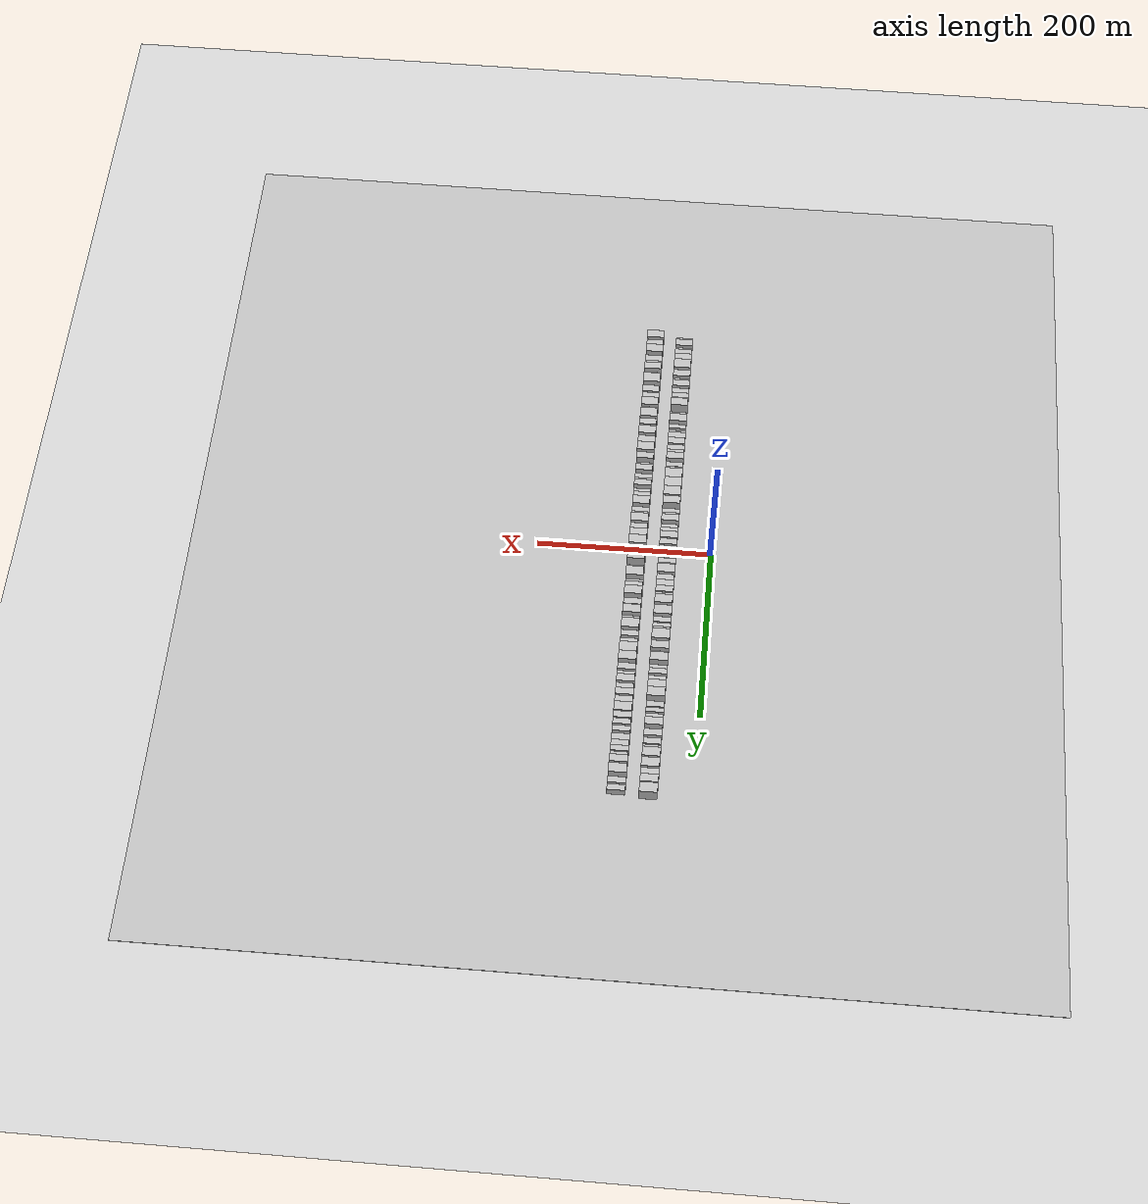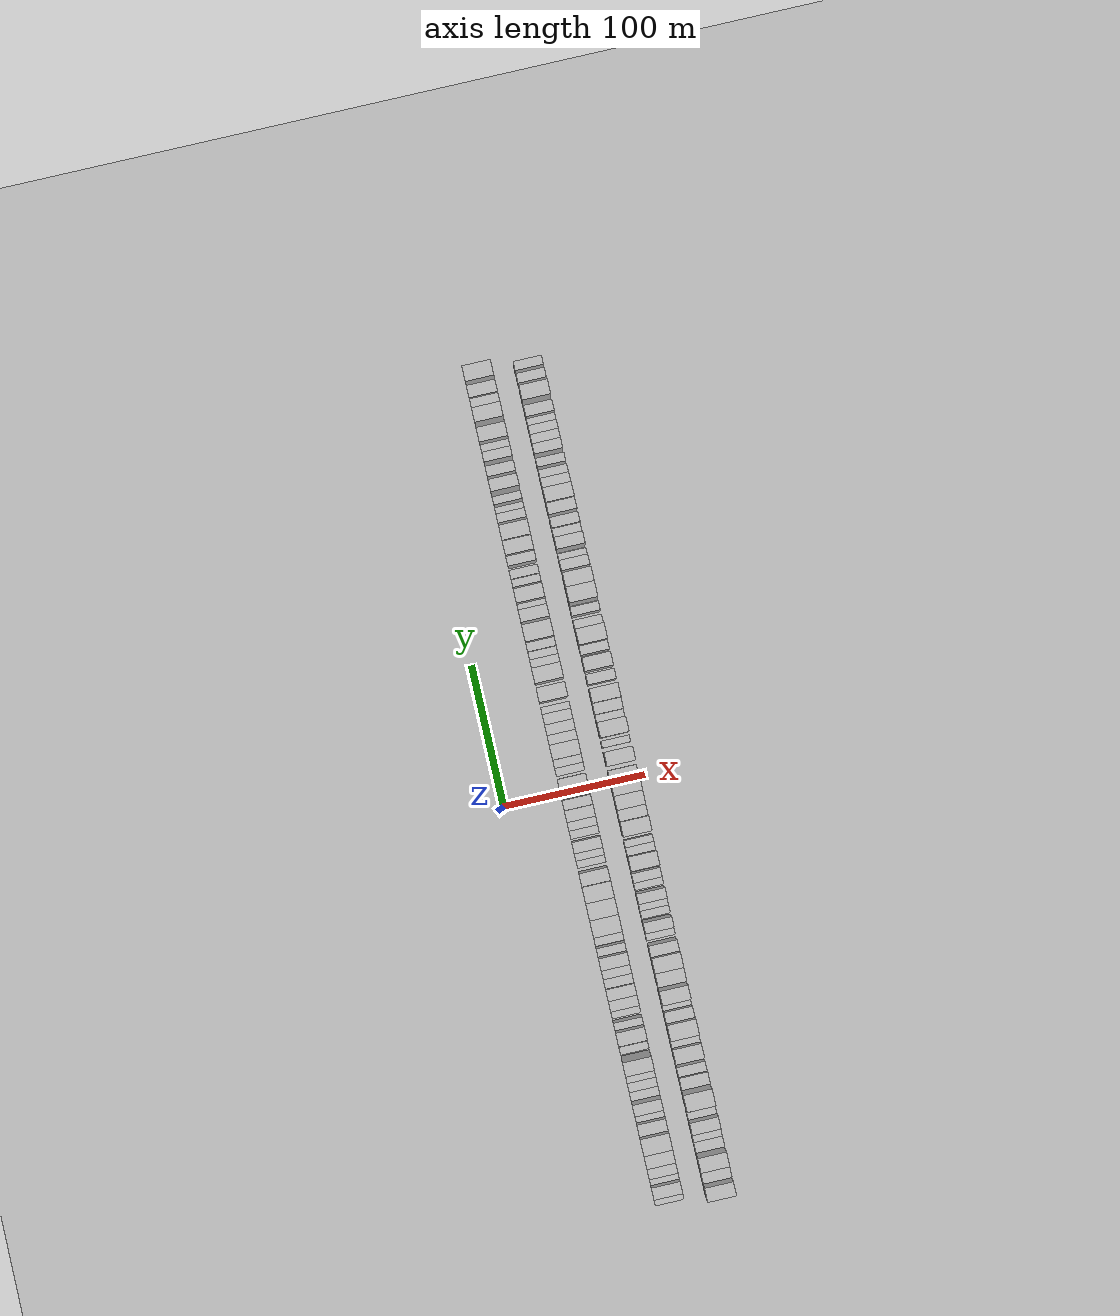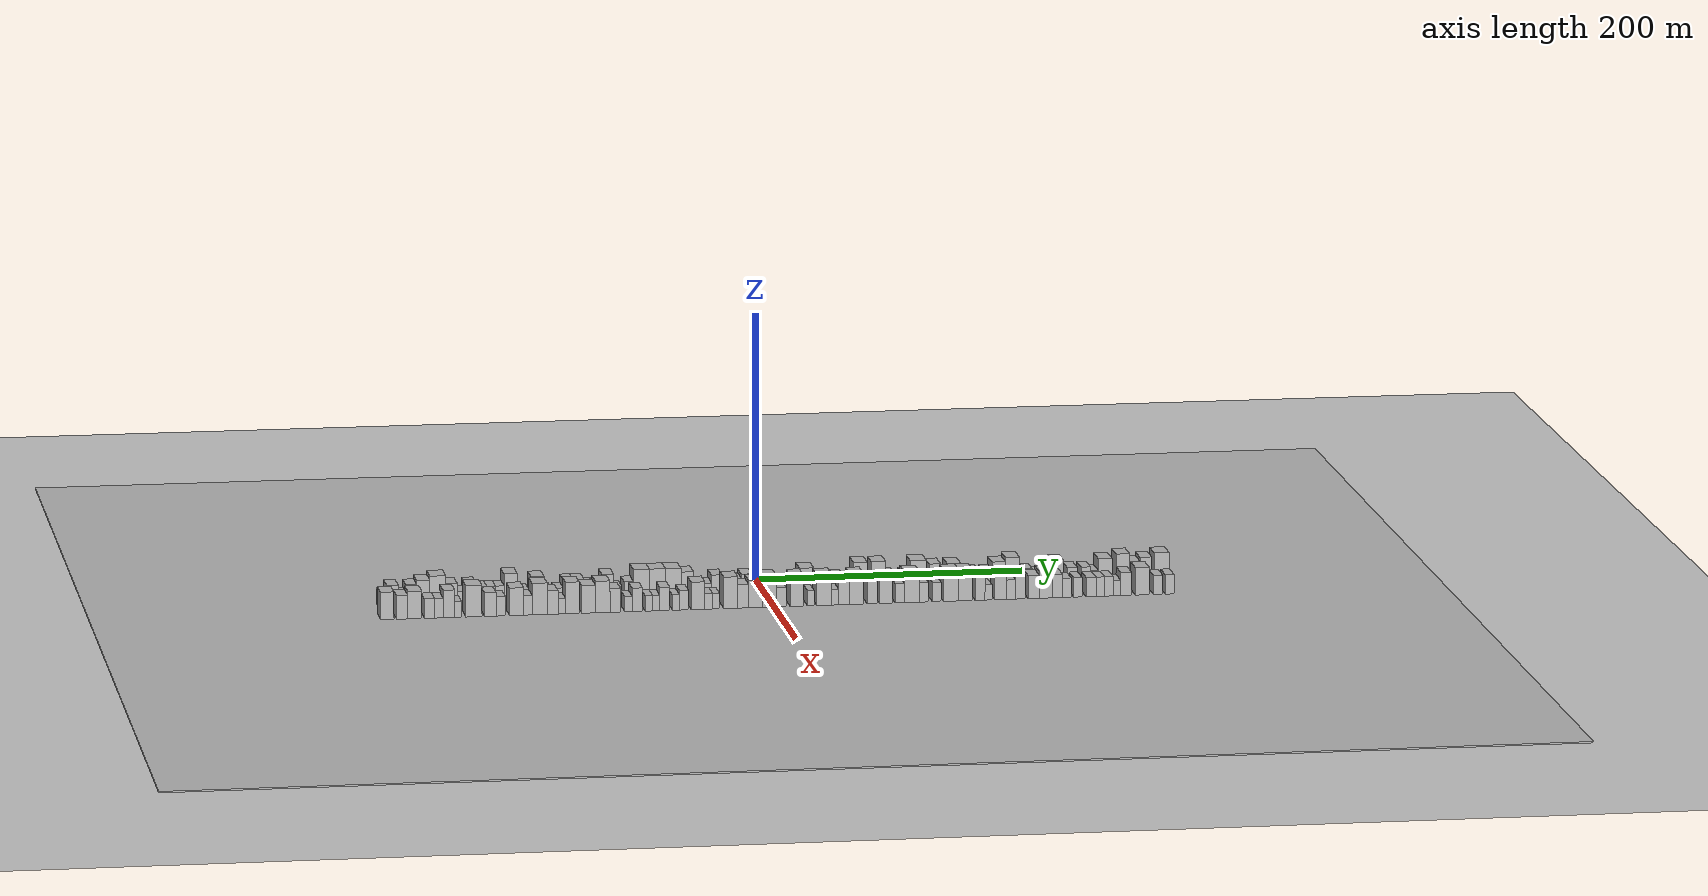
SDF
<?xml version="1.0" encoding="utf-8"?>

<sdf version="1.6">

   <world name="default">

      <gui fullscreen="0">

         <camera name="user_camera">

            <pose>-15 0 4.57585 0 0 0</pose>

            <view_controller>orbit</view_controller>

         </camera>

      </gui>

      <scene>

         <sky>

           <clouds>

             <speed>12</speed>

           </clouds>

         </sky>

         <ambient>0.4 0.4 0.4 1</ambient>

         <background>0.7 0.7 0.7 1</background>

         <shadows>1</shadows>

      </scene>

      <gravity>0 0 -9.8066</gravity>

      <magnetic_field>6e-06 2.3e-05 -4.2e-05</magnetic_field>

      <physics default="0" name="default_physics" type="ode">

         <ode>

            <solver>

               <type>quick</type>

               <iters>10</iters>

               <sor>1.0</sor>

               <use_dynamic_moi_rescaling>0</use_dynamic_moi_rescaling>

            </solver>

            <constraints>

               <cfm>0</cfm>

               <erp>0.2</erp>

               <contact_max_correcting_vel>100</contact_max_correcting_vel>

               <contact_surface_layer>0.001</contact_surface_layer>

            </constraints>

         </ode>

         <max_step_size>0.004</max_step_size>

         <real_time_factor>1</real_time_factor>

         <real_time_update_rate>250</real_time_update_rate>

      </physics>

      <light name="sun" type="directional">

         <cast_shadows>1</cast_shadows>

         <pose>0 0 10 0 0 0</pose>

         <diffuse>0.8 0.8 0.8 1</diffuse>

         <specular>0.2 0.2 0.2 1</specular>

         <attenuation>

            <range>1000</range>

            <constant>0.9</constant>

            <linear>0.01</linear>

            <quadratic>0.001</quadratic>

         </attenuation>

         <direction>-0.5 0.1 -0.9</direction>

      </light>

      <include>

         <name>ground_plane_1</name>

         <uri>model://HANNAS_ground_plane</uri>

         <pose>0 0 0  0 0 0</pose>

      </include>

      <include>

         <name>ground_plane_2</name>

         <uri>model://HANNAS_ground_plane</uri>

         <pose>100 0 0  0 0 0</pose>

      </include>

      <model name="building_1">

         <static>1</static>

         <pose frame="">50.0000 -284.1563 0 0.000000 0.000000 0.000000</pose>

         <link name="link">

            <pose frame="">0 0 6.00 0 0 0</pose>

            <collision name="collision">

               <geometry>

                  <box>

                     <size>20.0000 5.6873 12.0000</size>

                  </box>

               </geometry>

               <max_contacts>10</max_contacts>

               <surface>

                  <contact>

                     <ode/>

                  </contact>

                  <bounce/>

                  <friction>

                     <torsional>

                        <ode/>

                     </torsional>

                     <ode/>

                  </friction>

               </surface>

            </collision>

            <visual name="visual">

               <cast_shadows>0</cast_shadows>

               <geometry>

                  <box>

                     <size>20.0000 5.6873 12.0000</size>

                  </box>

               </geometry>

               <material>

                  <script>

                     <uri>model://HANNAS_wall/materials/scripts</uri>

                     <uri>model://HANNAS_wall/materials/textures</uri>

                     <name>vrc/HANNAS_wall</name>

                  </script>

               </material>

            </visual>

            <self_collide>0</self_collide>

            <enable_wind>0</enable_wind>

            <kinematic>0</kinematic>

         </link>

      </model>

      <model name="building_2">

         <static>1</static>

         <pose frame="">50.0000 -277.1323 0 0.000000 0.000000 0.000000</pose>

         <link name="link">

            <pose frame="">0 0 9.00 0 0 0</pose>

            <collision name="collision">

               <geometry>

                  <box>

                     <size>20.0000 8.3608 18.0000</size>

                  </box>

               </geometry>

               <max_contacts>10</max_contacts>

               <surface>

                  <contact>

                     <ode/>

                  </contact>

                  <bounce/>

                  <friction>

                     <torsional>

                        <ode/>

                     </torsional>

                     <ode/>

                  </friction>

               </surface>

            </collision>

            <visual name="visual">

               <cast_shadows>0</cast_shadows>

               <geometry>

                  <box>

                     <size>20.0000 8.3608 18.0000</size>

                  </box>

               </geometry>

               <material>

                  <script>

                     <uri>model://HANNAS_wall/materials/scripts</uri>

                     <uri>model://HANNAS_wall/materials/textures</uri>

                     <name>vrc/HANNAS_wall</name>

                  </script>

               </material>

            </visual>

            <self_collide>0</self_collide>

            <enable_wind>0</enable_wind>

            <kinematic>0</kinematic>

         </link>

      </model>

      <model name="building_3">

         <static>1</static>

         <pose frame="">50.0000 -270.0940 0 0.000000 0.000000 0.000000</pose>

         <link name="link">

            <pose frame="">0 0 6.00 0 0 0</pose>

            <collision name="collision">

               <geometry>

                  <box>

                     <size>20.0000 5.7157 12.0000</size>

                  </box>

               </geometry>

               <max_contacts>10</max_contacts>

               <surface>

                  <contact>

                     <ode/>

                  </contact>

                  <bounce/>

                  <friction>

                     <torsional>

                        <ode/>

                     </torsional>

                     <ode/>

                  </friction>

               </surface>

            </collision>

            <visual name="visual">

               <cast_shadows>0</cast_shadows>

               <geometry>

                  <box>

                     <size>20.0000 5.7157 12.0000</size>

                  </box>

               </geometry>

               <material>

                  <script>

                     <uri>model://HANNAS_wall/materials/scripts</uri>

                     <uri>model://HANNAS_wall/materials/textures</uri>

                     <name>vrc/HANNAS_wall</name>

                  </script>

               </material>

            </visual>

            <self_collide>0</self_collide>

            <enable_wind>0</enable_wind>

            <kinematic>0</kinematic>

         </link>

      </model>

      <model name="building_4">

         <static>1</static>

         <pose frame="">50.0000 -263.3036 0 0.000000 0.000000 0.000000</pose>

         <link name="link">

            <pose frame="">0 0 9.00 0 0 0</pose>

            <collision name="collision">

               <geometry>

                  <box>

                     <size>20.0000 7.8652 18.0000</size>

                  </box>

               </geometry>

               <max_contacts>10</max_contacts>

               <surface>

                  <contact>

                     <ode/>

                  </contact>

                  <bounce/>

                  <friction>

                     <torsional>

                        <ode/>

                     </torsional>

                     <ode/>

                  </friction>

               </surface>

            </collision>

            <visual name="visual">

               <cast_shadows>0</cast_shadows>

               <geometry>

                  <box>

                     <size>20.0000 7.8652 18.0000</size>

                  </box>

               </geometry>

               <material>

                  <script>

                     <uri>model://HANNAS_wall/materials/scripts</uri>

                     <uri>model://HANNAS_wall/materials/textures</uri>

                     <name>vrc/HANNAS_wall</name>

                  </script>

               </material>

            </visual>

            <self_collide>0</self_collide>

            <enable_wind>0</enable_wind>

            <kinematic>0</kinematic>

         </link>

      </model>

      <model name="building_5">

         <static>1</static>

         <pose frame="">50.0000 -254.5456 0 0.000000 0.000000 0.000000</pose>

         <link name="link">

            <pose frame="">0 0 10.50 0 0 0</pose>

            <collision name="collision">

               <geometry>

                  <box>

                     <size>20.0000 9.6508 21.0000</size>

                  </box>

               </geometry>

               <max_contacts>10</max_contacts>

               <surface>

                  <contact>

                     <ode/>

                  </contact>

                  <bounce/>

                  <friction>

                     <torsional>

                        <ode/>

                     </torsional>

                     <ode/>

                  </friction>

               </surface>

            </collision>

            <visual name="visual">

               <cast_shadows>0</cast_shadows>

               <geometry>

                  <box>

                     <size>20.0000 9.6508 21.0000</size>

                  </box>

               </geometry>

               <material>

                  <script>

                     <uri>model://HANNAS_wall/materials/scripts</uri>

                     <uri>model://HANNAS_wall/materials/textures</uri>

                     <name>vrc/HANNAS_wall</name>

                  </script>

               </material>

            </visual>

            <self_collide>0</self_collide>

            <enable_wind>0</enable_wind>

            <kinematic>0</kinematic>

         </link>

      </model>

      <model name="building_6">

         <static>1</static>

         <pose frame="">50.0000 -243.8503 0 0.000000 0.000000 0.000000</pose>

         <link name="link">

            <pose frame="">0 0 12.00 0 0 0</pose>

            <collision name="collision">

               <geometry>

                  <box>

                     <size>20.0000 11.7398 24.0000</size>

                  </box>

               </geometry>

               <max_contacts>10</max_contacts>

               <surface>

                  <contact>

                     <ode/>

                  </contact>

                  <bounce/>

                  <friction>

                     <torsional>

                        <ode/>

                     </torsional>

                     <ode/>

                  </friction>

               </surface>

            </collision>

            <visual name="visual">

               <cast_shadows>0</cast_shadows>

               <geometry>

                  <box>

                     <size>20.0000 11.7398 24.0000</size>

                  </box>

               </geometry>

               <material>

                  <script>

                     <uri>model://HANNAS_wall/materials/scripts</uri>

                     <uri>model://HANNAS_wall/materials/textures</uri>

                     <name>vrc/HANNAS_wall</name>

                  </script>

               </material>

            </visual>

            <self_collide>0</self_collide>

            <enable_wind>0</enable_wind>

            <kinematic>0</kinematic>

         </link>

      </model>

      <model name="building_7">

         <static>1</static>

         <pose frame="">50.0000 -233.7689 0 0.000000 0.000000 0.000000</pose>

         <link name="link">

            <pose frame="">0 0 9.00 0 0 0</pose>

            <collision name="collision">

               <geometry>

                  <box>

                     <size>20.0000 8.4229 18.0000</size>

                  </box>

               </geometry>

               <max_contacts>10</max_contacts>

               <surface>

                  <contact>

                     <ode/>

                  </contact>

                  <bounce/>

                  <friction>

                     <torsional>

                        <ode/>

                     </torsional>

                     <ode/>

                  </friction>

               </surface>

            </collision>

            <visual name="visual">

               <cast_shadows>0</cast_shadows>

               <geometry>

                  <box>

                     <size>20.0000 8.4229 18.0000</size>

                  </box>

               </geometry>

               <material>

                  <script>

                     <uri>model://HANNAS_wall/materials/scripts</uri>

                     <uri>model://HANNAS_wall/materials/textures</uri>

                     <name>vrc/HANNAS_wall</name>

                  </script>

               </material>

            </visual>

            <self_collide>0</self_collide>

            <enable_wind>0</enable_wind>

            <kinematic>0</kinematic>

         </link>

      </model>

      <model name="building_8">

         <static>1</static>

         <pose frame="">50.0000 -226.7244 0 0.000000 0.000000 0.000000</pose>

         <link name="link">

            <pose frame="">0 0 6.00 0 0 0</pose>

            <collision name="collision">

               <geometry>

                  <box>

                     <size>20.0000 5.6663 12.0000</size>

                  </box>

               </geometry>

               <max_contacts>10</max_contacts>

               <surface>

                  <contact>

                     <ode/>

                  </contact>

                  <bounce/>

                  <friction>

                     <torsional>

                        <ode/>

                     </torsional>

                     <ode/>

                  </friction>

               </surface>

            </collision>

            <visual name="visual">

               <cast_shadows>0</cast_shadows>

               <geometry>

                  <box>

                     <size>20.0000 5.6663 12.0000</size>

                  </box>

               </geometry>

               <material>

                  <script>

                     <uri>model://HANNAS_wall/materials/scripts</uri>

                     <uri>model://HANNAS_wall/materials/textures</uri>

                     <name>vrc/HANNAS_wall</name>

                  </script>

               </material>

            </visual>

            <self_collide>0</self_collide>

            <enable_wind>0</enable_wind>

            <kinematic>0</kinematic>

         </link>

      </model>

      <model name="building_9">

         <static>1</static>

         <pose frame="">50.0000 -219.8994 0 0.000000 0.000000 0.000000</pose>

         <link name="link">

            <pose frame="">0 0 9.00 0 0 0</pose>

            <collision name="collision">

               <geometry>

                  <box>

                     <size>20.0000 7.9838 18.0000</size>

                  </box>

               </geometry>

               <max_contacts>10</max_contacts>

               <surface>

                  <contact>

                     <ode/>

                  </contact>

                  <bounce/>

                  <friction>

                     <torsional>

                        <ode/>

                     </torsional>

                     <ode/>

                  </friction>

               </surface>

            </collision>

            <visual name="visual">

               <cast_shadows>0</cast_shadows>

               <geometry>

                  <box>

                     <size>20.0000 7.9838 18.0000</size>

                  </box>

               </geometry>

               <material>

                  <script>

                     <uri>model://HANNAS_wall/materials/scripts</uri>

                     <uri>model://HANNAS_wall/materials/textures</uri>

                     <name>vrc/HANNAS_wall</name>

                  </script>

               </material>

            </visual>

            <self_collide>0</self_collide>

            <enable_wind>0</enable_wind>

            <kinematic>0</kinematic>

         </link>

      </model>

      <model name="building_10">

         <static>1</static>

         <pose frame="">50.0000 -210.8327 0 0.000000 0.000000 0.000000</pose>

         <link name="link">

            <pose frame="">0 0 7.50 0 0 0</pose>

            <collision name="collision">

               <geometry>

                  <box>

                     <size>20.0000 6.1495 15.0000</size>

                  </box>

               </geometry>

               <max_contacts>10</max_contacts>

               <surface>

                  <contact>

                     <ode/>

                  </contact>

                  <bounce/>

                  <friction>

                     <torsional>

                        <ode/>

                     </torsional>

                     <ode/>

                  </friction>

               </surface>

            </collision>

            <visual name="visual">

               <cast_shadows>0</cast_shadows>

               <geometry>

                  <box>

                     <size>20.0000 6.1495 15.0000</size>

                  </box>

               </geometry>

               <material>

                  <script>

                     <uri>model://HANNAS_wall/materials/scripts</uri>

                     <uri>model://HANNAS_wall/materials/textures</uri>

                     <name>vrc/HANNAS_wall</name>

                  </script>

               </material>

            </visual>

            <self_collide>0</self_collide>

            <enable_wind>0</enable_wind>

            <kinematic>0</kinematic>

         </link>

      </model>

      <model name="building_11">

         <static>1</static>

         <pose frame="">50.0000 -204.6135 0 0.000000 0.000000 0.000000</pose>

         <link name="link">

            <pose frame="">0 0 7.50 0 0 0</pose>

            <collision name="collision">

               <geometry>

                  <box>

                     <size>20.0000 6.2890 15.0000</size>

                  </box>

               </geometry>

               <max_contacts>10</max_contacts>

               <surface>

                  <contact>

                     <ode/>

                  </contact>

                  <bounce/>

                  <friction>

                     <torsional>

                        <ode/>

                     </torsional>

                     <ode/>

                  </friction>

               </surface>

            </collision>

            <visual name="visual">

               <cast_shadows>0</cast_shadows>

               <geometry>

                  <box>

                     <size>20.0000 6.2890 15.0000</size>

                  </box>

               </geometry>

               <material>

                  <script>

                     <uri>model://HANNAS_wall/materials/scripts</uri>

                     <uri>model://HANNAS_wall/materials/textures</uri>

                     <name>vrc/HANNAS_wall</name>

                  </script>

               </material>

            </visual>

            <self_collide>0</self_collide>

            <enable_wind>0</enable_wind>

            <kinematic>0</kinematic>

         </link>

      </model>

      <model name="building_12">

         <static>1</static>

         <pose frame="">50.0000 -198.2615 0 0.000000 0.000000 0.000000</pose>

         <link name="link">

            <pose frame="">0 0 7.50 0 0 0</pose>

            <collision name="collision">

               <geometry>

                  <box>

                     <size>20.0000 6.4150 15.0000</size>

                  </box>

               </geometry>

               <max_contacts>10</max_contacts>

               <surface>

                  <contact>

                     <ode/>

                  </contact>

                  <bounce/>

                  <friction>

                     <torsional>

                        <ode/>

                     </torsional>

                     <ode/>

                  </friction>

               </surface>

            </collision>

            <visual name="visual">

               <cast_shadows>0</cast_shadows>

               <geometry>

                  <box>

                     <size>20.0000 6.4150 15.0000</size>

                  </box>

               </geometry>

               <material>

                  <script>

                     <uri>model://HANNAS_wall/materials/scripts</uri>

                     <uri>model://HANNAS_wall/materials/textures</uri>

                     <name>vrc/HANNAS_wall</name>

                  </script>

               </material>

            </visual>

            <self_collide>0</self_collide>

            <enable_wind>0</enable_wind>

            <kinematic>0</kinematic>

         </link>

      </model>

      <model name="building_13">

         <static>1</static>

         <pose frame="">50.0000 -190.1850 0 0.000000 0.000000 0.000000</pose>

         <link name="link">

            <pose frame="">0 0 12.00 0 0 0</pose>

            <collision name="collision">

               <geometry>

                  <box>

                     <size>20.0000 9.7380 24.0000</size>

                  </box>

               </geometry>

               <max_contacts>10</max_contacts>

               <surface>

                  <contact>

                     <ode/>

                  </contact>

                  <bounce/>

                  <friction>

                     <torsional>

                        <ode/>

                     </torsional>

                     <ode/>

                  </friction>

               </surface>

            </collision>

            <visual name="visual">

               <cast_shadows>0</cast_shadows>

               <geometry>

                  <box>

                     <size>20.0000 9.7380 24.0000</size>

                  </box>

               </geometry>

               <material>

                  <script>

                     <uri>model://HANNAS_wall/materials/scripts</uri>

                     <uri>model://HANNAS_wall/materials/textures</uri>

                     <name>vrc/HANNAS_wall</name>

                  </script>

               </material>

            </visual>

            <self_collide>0</self_collide>

            <enable_wind>0</enable_wind>

            <kinematic>0</kinematic>

         </link>

      </model>

      <model name="building_14">

         <static>1</static>

         <pose frame="">50.0000 -179.6250 0 0.000000 0.000000 0.000000</pose>

         <link name="link">

            <pose frame="">0 0 6.00 0 0 0</pose>

            <collision name="collision">

               <geometry>

                  <box>

                     <size>20.0000 5.3820 12.0000</size>

                  </box>

               </geometry>

               <max_contacts>10</max_contacts>

               <surface>

                  <contact>

                     <ode/>

                  </contact>

                  <bounce/>

                  <friction>

                     <torsional>

                        <ode/>

                     </torsional>

                     <ode/>

                  </friction>

               </surface>

            </collision>

            <visual name="visual">

               <cast_shadows>0</cast_shadows>

               <geometry>

                  <box>

                     <size>20.0000 5.3820 12.0000</size>

                  </box>

               </geometry>

               <material>

                  <script>

                     <uri>model://HANNAS_wall/materials/scripts</uri>

                     <uri>model://HANNAS_wall/materials/textures</uri>

                     <name>vrc/HANNAS_wall</name>

                  </script>

               </material>

            </visual>

            <self_collide>0</self_collide>

            <enable_wind>0</enable_wind>

            <kinematic>0</kinematic>

         </link>

      </model>

      <model name="building_15">

         <static>1</static>

         <pose frame="">50.0000 -170.2009 0 0.000000 0.000000 0.000000</pose>

         <link name="link">

            <pose frame="">0 0 10.50 0 0 0</pose>

            <collision name="collision">

               <geometry>

                  <box>

                     <size>20.0000 9.4661 21.0000</size>

                  </box>

               </geometry>

               <max_contacts>10</max_contacts>

               <surface>

                  <contact>

                     <ode/>

                  </contact>

                  <bounce/>

                  <friction>

                     <torsional>

                        <ode/>

                     </torsional>

                     <ode/>

                  </friction>

               </surface>

            </collision>

            <visual name="visual">

               <cast_shadows>0</cast_shadows>

               <geometry>

                  <box>

                     <size>20.0000 9.4661 21.0000</size>

                  </box>

               </geometry>

               <material>

                  <script>

                     <uri>model://HANNAS_wall/materials/scripts</uri>

                     <uri>model://HANNAS_wall/materials/textures</uri>

                     <name>vrc/HANNAS_wall</name>

                  </script>

               </material>

            </visual>

            <self_collide>0</self_collide>

            <enable_wind>0</enable_wind>

            <kinematic>0</kinematic>

         </link>

      </model>

      <model name="building_16">

         <static>1</static>

         <pose frame="">50.0000 -162.8109 0 0.000000 0.000000 0.000000</pose>

         <link name="link">

            <pose frame="">0 0 6.00 0 0 0</pose>

            <collision name="collision">

               <geometry>

                  <box>

                     <size>20.0000 5.3140 12.0000</size>

                  </box>

               </geometry>

               <max_contacts>10</max_contacts>

               <surface>

                  <contact>

                     <ode/>

                  </contact>

                  <bounce/>

                  <friction>

                     <torsional>

                        <ode/>

                     </torsional>

                     <ode/>

                  </friction>

               </surface>

            </collision>

            <visual name="visual">

               <cast_shadows>0</cast_shadows>

               <geometry>

                  <box>

                     <size>20.0000 5.3140 12.0000</size>

                  </box>

               </geometry>

               <material>

                  <script>

                     <uri>model://HANNAS_wall/materials/scripts</uri>

                     <uri>model://HANNAS_wall/materials/textures</uri>

                     <name>vrc/HANNAS_wall</name>

                  </script>

               </material>

            </visual>

            <self_collide>0</self_collide>

            <enable_wind>0</enable_wind>

            <kinematic>0</kinematic>

         </link>

      </model>

      <model name="building_17">

         <static>1</static>

         <pose frame="">50.0000 -154.2552 0 0.000000 0.000000 0.000000</pose>

         <link name="link">

            <pose frame="">0 0 6.00 0 0 0</pose>

            <collision name="collision">

               <geometry>

                  <box>

                     <size>20.0000 5.7974 12.0000</size>

                  </box>

               </geometry>

               <max_contacts>10</max_contacts>

               <surface>

                  <contact>

                     <ode/>

                  </contact>

                  <bounce/>

                  <friction>

                     <torsional>

                        <ode/>

                     </torsional>

                     <ode/>

                  </friction>

               </surface>

            </collision>

            <visual name="visual">

               <cast_shadows>0</cast_shadows>

               <geometry>

                  <box>

                     <size>20.0000 5.7974 12.0000</size>

                  </box>

               </geometry>

               <material>

                  <script>

                     <uri>model://HANNAS_wall/materials/scripts</uri>

                     <uri>model://HANNAS_wall/materials/textures</uri>

                     <name>vrc/HANNAS_wall</name>

                  </script>

               </material>

            </visual>

            <self_collide>0</self_collide>

            <enable_wind>0</enable_wind>

            <kinematic>0</kinematic>

         </link>

      </model>

      <model name="building_18">

         <static>1</static>

         <pose frame="">50.0000 -147.7328 0 0.000000 0.000000 0.000000</pose>

         <link name="link">

            <pose frame="">0 0 9.00 0 0 0</pose>

            <collision name="collision">

               <geometry>

                  <box>

                     <size>20.0000 7.2473 18.0000</size>

                  </box>

               </geometry>

               <max_contacts>10</max_contacts>

               <surface>

                  <contact>

                     <ode/>

                  </contact>

                  <bounce/>

                  <friction>

                     <torsional>

                        <ode/>

                     </torsional>

                     <ode/>

                  </friction>

               </surface>

            </collision>

            <visual name="visual">

               <cast_shadows>0</cast_shadows>

               <geometry>

                  <box>

                     <size>20.0000 7.2473 18.0000</size>

                  </box>

               </geometry>

               <material>

                  <script>

                     <uri>model://HANNAS_wall/materials/scripts</uri>

                     <uri>model://HANNAS_wall/materials/textures</uri>

                     <name>vrc/HANNAS_wall</name>

                  </script>

               </material>

            </visual>

            <self_collide>0</self_collide>

            <enable_wind>0</enable_wind>

            <kinematic>0</kinematic>

         </link>

      </model>

      <model name="building_19">

         <static>1</static>

         <pose frame="">50.0000 -140.0425 0 0.000000 0.000000 0.000000</pose>

         <link name="link">

            <pose frame="">0 0 9.00 0 0 0</pose>

            <collision name="collision">

               <geometry>

                  <box>

                     <size>20.0000 8.1334 18.0000</size>

                  </box>

               </geometry>

               <max_contacts>10</max_contacts>

               <surface>

                  <contact>

                     <ode/>

                  </contact>

                  <bounce/>

                  <friction>

                     <torsional>

                        <ode/>

                     </torsional>

                     <ode/>

                  </friction>

               </surface>

            </collision>

            <visual name="visual">

               <cast_shadows>0</cast_shadows>

               <geometry>

                  <box>

                     <size>20.0000 8.1334 18.0000</size>

                  </box>

               </geometry>

               <material>

                  <script>

                     <uri>model://HANNAS_wall/materials/scripts</uri>

                     <uri>model://HANNAS_wall/materials/textures</uri>

                     <name>vrc/HANNAS_wall</name>

                  </script>

               </material>

            </visual>

            <self_collide>0</self_collide>

            <enable_wind>0</enable_wind>

            <kinematic>0</kinematic>

         </link>

      </model>

      <model name="building_20">

         <static>1</static>

         <pose frame="">50.0000 -132.7113 0 0.000000 0.000000 0.000000</pose>

         <link name="link">

            <pose frame="">0 0 7.50 0 0 0</pose>

            <collision name="collision">

               <geometry>

                  <box>

                     <size>20.0000 6.5290 15.0000</size>

                  </box>

               </geometry>

               <max_contacts>10</max_contacts>

               <surface>

                  <contact>

                     <ode/>

                  </contact>

                  <bounce/>

                  <friction>

                     <torsional>

                        <ode/>

                     </torsional>

                     <ode/>

                  </friction>

               </surface>

            </collision>

            <visual name="visual">

               <cast_shadows>0</cast_shadows>

               <geometry>

                  <box>

                     <size>20.0000 6.5290 15.0000</size>

                  </box>

               </geometry>

               <material>

                  <script>

                     <uri>model://HANNAS_wall/materials/scripts</uri>

                     <uri>model://HANNAS_wall/materials/textures</uri>

                     <name>vrc/HANNAS_wall</name>

                  </script>

               </material>

            </visual>

            <self_collide>0</self_collide>

            <enable_wind>0</enable_wind>

            <kinematic>0</kinematic>

         </link>

      </model>

      <model name="building_21">

         <static>1</static>

         <pose frame="">50.0000 -125.9997 0 0.000000 0.000000 0.000000</pose>

         <link name="link">

            <pose frame="">0 0 7.50 0 0 0</pose>

            <collision name="collision">

               <geometry>

                  <box>

                     <size>20.0000 6.8943 15.0000</size>

                  </box>

               </geometry>

               <max_contacts>10</max_contacts>

               <surface>

                  <contact>

                     <ode/>

                  </contact>

                  <bounce/>

                  <friction>

                     <torsional>

                        <ode/>

                     </torsional>

                     <ode/>

                  </friction>

               </surface>

            </collision>

            <visual name="visual">

               <cast_shadows>0</cast_shadows>

               <geometry>

                  <box>

                     <size>20.0000 6.8943 15.0000</size>

                  </box>

               </geometry>

               <material>

                  <script>

                     <uri>model://HANNAS_wall/materials/scripts</uri>

                     <uri>model://HANNAS_wall/materials/textures</uri>

                     <name>vrc/HANNAS_wall</name>

                  </script>

               </material>

            </visual>

            <self_collide>0</self_collide>

            <enable_wind>0</enable_wind>

            <kinematic>0</kinematic>

         </link>

      </model>

      <model name="building_22">

         <static>1</static>

         <pose frame="">50.0000 -118.2893 0 0.000000 0.000000 0.000000</pose>

         <link name="link">

            <pose frame="">0 0 10.50 0 0 0</pose>

            <collision name="collision">

               <geometry>

                  <box>

                     <size>20.0000 8.5265 21.0000</size>

                  </box>

               </geometry>

               <max_contacts>10</max_contacts>

               <surface>

                  <contact>

                     <ode/>

                  </contact>

                  <bounce/>

                  <friction>

                     <torsional>

                        <ode/>

                     </torsional>

                     <ode/>

                  </friction>

               </surface>

            </collision>

            <visual name="visual">

               <cast_shadows>0</cast_shadows>

               <geometry>

                  <box>

                     <size>20.0000 8.5265 21.0000</size>

                  </box>

               </geometry>

               <material>

                  <script>

                     <uri>model://HANNAS_wall/materials/scripts</uri>

                     <uri>model://HANNAS_wall/materials/textures</uri>

                     <name>vrc/HANNAS_wall</name>

                  </script>

               </material>

            </visual>

            <self_collide>0</self_collide>

            <enable_wind>0</enable_wind>

            <kinematic>0</kinematic>

         </link>

      </model>

      <model name="building_23">

         <static>1</static>

         <pose frame="">50.0000 -111.1062 0 0.000000 0.000000 0.000000</pose>

         <link name="link">

            <pose frame="">0 0 6.00 0 0 0</pose>

            <collision name="collision">

               <geometry>

                  <box>

                     <size>20.0000 5.8397 12.0000</size>

                  </box>

               </geometry>

               <max_contacts>10</max_contacts>

               <surface>

                  <contact>

                     <ode/>

                  </contact>

                  <bounce/>

                  <friction>

                     <torsional>

                        <ode/>

                     </torsional>

                     <ode/>

                  </friction>

               </surface>

            </collision>

            <visual name="visual">

               <cast_shadows>0</cast_shadows>

               <geometry>

                  <box>

                     <size>20.0000 5.8397 12.0000</size>

                  </box>

               </geometry>

               <material>

                  <script>

                     <uri>model://HANNAS_wall/materials/scripts</uri>

                     <uri>model://HANNAS_wall/materials/textures</uri>

                     <name>vrc/HANNAS_wall</name>

                  </script>

               </material>

            </visual>

            <self_collide>0</self_collide>

            <enable_wind>0</enable_wind>

            <kinematic>0</kinematic>

         </link>

      </model>

      <model name="building_24">

         <static>1</static>

         <pose frame="">50.0000 -102.7975 0 0.000000 0.000000 0.000000</pose>

         <link name="link">

            <pose frame="">0 0 7.50 0 0 0</pose>

            <collision name="collision">

               <geometry>

                  <box>

                     <size>20.0000 6.7777 15.0000</size>

                  </box>

               </geometry>

               <max_contacts>10</max_contacts>

               <surface>

                  <contact>

                     <ode/>

                  </contact>

                  <bounce/>

                  <friction>

                     <torsional>

                        <ode/>

                     </torsional>

                     <ode/>

                  </friction>

               </surface>

            </collision>

            <visual name="visual">

               <cast_shadows>0</cast_shadows>

               <geometry>

                  <box>

                     <size>20.0000 6.7777 15.0000</size>

                  </box>

               </geometry>

               <material>

                  <script>

                     <uri>model://HANNAS_wall/materials/scripts</uri>

                     <uri>model://HANNAS_wall/materials/textures</uri>

                     <name>vrc/HANNAS_wall</name>

                  </script>

               </material>

            </visual>

            <self_collide>0</self_collide>

            <enable_wind>0</enable_wind>

            <kinematic>0</kinematic>

         </link>

      </model>

      <model name="building_25">

         <static>1</static>

         <pose frame="">50.0000 -93.4668 0 0.000000 0.000000 0.000000</pose>

         <link name="link">

            <pose frame="">0 0 12.00 0 0 0</pose>

            <collision name="collision">

               <geometry>

                  <box>

                     <size>20.0000 11.8837 24.0000</size>

                  </box>

               </geometry>

               <max_contacts>10</max_contacts>

               <surface>

                  <contact>

                     <ode/>

                  </contact>

                  <bounce/>

                  <friction>

                     <torsional>

                        <ode/>

                     </torsional>

                     <ode/>

                  </friction>

               </surface>

            </collision>

            <visual name="visual">

               <cast_shadows>0</cast_shadows>

               <geometry>

                  <box>

                     <size>20.0000 11.8837 24.0000</size>

                  </box>

               </geometry>

               <material>

                  <script>

                     <uri>model://HANNAS_wall/materials/scripts</uri>

                     <uri>model://HANNAS_wall/materials/textures</uri>

                     <name>vrc/HANNAS_wall</name>

                  </script>

               </material>

            </visual>

            <self_collide>0</self_collide>

            <enable_wind>0</enable_wind>

            <kinematic>0</kinematic>

         </link>

      </model>

      <model name="building_26">

         <static>1</static>

         <pose frame="">50.0000 -81.6182 0 0.000000 0.000000 0.000000</pose>

         <link name="link">

            <pose frame="">0 0 12.00 0 0 0</pose>

            <collision name="collision">

               <geometry>

                  <box>

                     <size>20.0000 11.8136 24.0000</size>

                  </box>

               </geometry>

               <max_contacts>10</max_contacts>

               <surface>

                  <contact>

                     <ode/>

                  </contact>

                  <bounce/>

                  <friction>

                     <torsional>

                        <ode/>

                     </torsional>

                     <ode/>

                  </friction>

               </surface>

            </collision>

            <visual name="visual">

               <cast_shadows>0</cast_shadows>

               <geometry>

                  <box>

                     <size>20.0000 11.8136 24.0000</size>

                  </box>

               </geometry>

               <material>

                  <script>

                     <uri>model://HANNAS_wall/materials/scripts</uri>

                     <uri>model://HANNAS_wall/materials/textures</uri>

                     <name>vrc/HANNAS_wall</name>

                  </script>

               </material>

            </visual>

            <self_collide>0</self_collide>

            <enable_wind>0</enable_wind>

            <kinematic>0</kinematic>

         </link>

      </model>

      <model name="building_27">

         <static>1</static>

         <pose frame="">50.0000 -70.0026 0 0.000000 0.000000 0.000000</pose>

         <link name="link">

            <pose frame="">0 0 12.00 0 0 0</pose>

            <collision name="collision">

               <geometry>

                  <box>

                     <size>20.0000 11.4176 24.0000</size>

                  </box>

               </geometry>

               <max_contacts>10</max_contacts>

               <surface>

                  <contact>

                     <ode/>

                  </contact>

                  <bounce/>

                  <friction>

                     <torsional>

                        <ode/>

                     </torsional>

                     <ode/>

                  </friction>

               </surface>

            </collision>

            <visual name="visual">

               <cast_shadows>0</cast_shadows>

               <geometry>

                  <box>

                     <size>20.0000 11.4176 24.0000</size>

                  </box>

               </geometry>

               <material>

                  <script>

                     <uri>model://HANNAS_wall/materials/scripts</uri>

                     <uri>model://HANNAS_wall/materials/textures</uri>

                     <name>vrc/HANNAS_wall</name>

                  </script>

               </material>

            </visual>

            <self_collide>0</self_collide>

            <enable_wind>0</enable_wind>

            <kinematic>0</kinematic>

         </link>

      </model>

      <model name="building_28">

         <static>1</static>

         <pose frame="">50.0000 -59.6757 0 0.000000 0.000000 0.000000</pose>

         <link name="link">

            <pose frame="">0 0 10.50 0 0 0</pose>

            <collision name="collision">

               <geometry>

                  <box>

                     <size>20.0000 9.2361 21.0000</size>

                  </box>

               </geometry>

               <max_contacts>10</max_contacts>

               <surface>

                  <contact>

                     <ode/>

                  </contact>

                  <bounce/>

                  <friction>

                     <torsional>

                        <ode/>

                     </torsional>

                     <ode/>

                  </friction>

               </surface>

            </collision>

            <visual name="visual">

               <cast_shadows>0</cast_shadows>

               <geometry>

                  <box>

                     <size>20.0000 9.2361 21.0000</size>

                  </box>

               </geometry>

               <material>

                  <script>

                     <uri>model://HANNAS_wall/materials/scripts</uri>

                     <uri>model://HANNAS_wall/materials/textures</uri>

                     <name>vrc/HANNAS_wall</name>

                  </script>

               </material>

            </visual>

            <self_collide>0</self_collide>

            <enable_wind>0</enable_wind>

            <kinematic>0</kinematic>

         </link>

      </model>

      <model name="building_29">

         <static>1</static>

         <pose frame="">50.0000 -49.5209 0 0.000000 0.000000 0.000000</pose>

         <link name="link">

            <pose frame="">0 0 6.00 0 0 0</pose>

            <collision name="collision">

               <geometry>

                  <box>

                     <size>20.0000 5.0735 12.0000</size>

                  </box>

               </geometry>

               <max_contacts>10</max_contacts>

               <surface>

                  <contact>

                     <ode/>

                  </contact>

                  <bounce/>

                  <friction>

                     <torsional>

                        <ode/>

                     </torsional>

                     <ode/>

                  </friction>

               </surface>

            </collision>

            <visual name="visual">

               <cast_shadows>0</cast_shadows>

               <geometry>

                  <box>

                     <size>20.0000 5.0735 12.0000</size>

                  </box>

               </geometry>

               <material>

                  <script>

                     <uri>model://HANNAS_wall/materials/scripts</uri>

                     <uri>model://HANNAS_wall/materials/textures</uri>

                     <name>vrc/HANNAS_wall</name>

                  </script>

               </material>

            </visual>

            <self_collide>0</self_collide>

            <enable_wind>0</enable_wind>

            <kinematic>0</kinematic>

         </link>

      </model>

      <model name="building_30">

         <static>1</static>

         <pose frame="">50.0000 -44.2629 0 0.000000 0.000000 0.000000</pose>

         <link name="link">

            <pose frame="">0 0 6.00 0 0 0</pose>

            <collision name="collision">

               <geometry>

                  <box>

                     <size>20.0000 5.4425 12.0000</size>

                  </box>

               </geometry>

               <max_contacts>10</max_contacts>

               <surface>

                  <contact>

                     <ode/>

                  </contact>

                  <bounce/>

                  <friction>

                     <torsional>

                        <ode/>

                     </torsional>

                     <ode/>

                  </friction>

               </surface>

            </collision>

            <visual name="visual">

               <cast_shadows>0</cast_shadows>

               <geometry>

                  <box>

                     <size>20.0000 5.4425 12.0000</size>

                  </box>

               </geometry>

               <material>

                  <script>

                     <uri>model://HANNAS_wall/materials/scripts</uri>

                     <uri>model://HANNAS_wall/materials/textures</uri>

                     <name>vrc/HANNAS_wall</name>

                  </script>

               </material>

            </visual>

            <self_collide>0</self_collide>

            <enable_wind>0</enable_wind>

            <kinematic>0</kinematic>

         </link>

      </model>

      <model name="building_31">

         <static>1</static>

         <pose frame="">50.0000 -37.5939 0 0.000000 0.000000 0.000000</pose>

         <link name="link">

            <pose frame="">0 0 9.00 0 0 0</pose>

            <collision name="collision">

               <geometry>

                  <box>

                     <size>20.0000 7.8954 18.0000</size>

                  </box>

               </geometry>

               <max_contacts>10</max_contacts>

               <surface>

                  <contact>

                     <ode/>

                  </contact>

                  <bounce/>

                  <friction>

                     <torsional>

                        <ode/>

                     </torsional>

                     <ode/>

                  </friction>

               </surface>

            </collision>

            <visual name="visual">

               <cast_shadows>0</cast_shadows>

               <geometry>

                  <box>

                     <size>20.0000 7.8954 18.0000</size>

                  </box>

               </geometry>

               <material>

                  <script>

                     <uri>model://HANNAS_wall/materials/scripts</uri>

                     <uri>model://HANNAS_wall/materials/textures</uri>

                     <name>vrc/HANNAS_wall</name>

                  </script>

               </material>

            </visual>

            <self_collide>0</self_collide>

            <enable_wind>0</enable_wind>

            <kinematic>0</kinematic>

         </link>

      </model>

      <model name="building_32">

         <static>1</static>

         <pose frame="">50.0000 -28.7165 0 0.000000 0.000000 0.000000</pose>

         <link name="link">

            <pose frame="">0 0 6.00 0 0 0</pose>

            <collision name="collision">

               <geometry>

                  <box>

                     <size>20.0000 5.8594 12.0000</size>

                  </box>

               </geometry>

               <max_contacts>10</max_contacts>

               <surface>

                  <contact>

                     <ode/>

                  </contact>

                  <bounce/>

                  <friction>

                     <torsional>

                        <ode/>

                     </torsional>

                     <ode/>

                  </friction>

               </surface>

            </collision>

            <visual name="visual">

               <cast_shadows>0</cast_shadows>

               <geometry>

                  <box>

                     <size>20.0000 5.8594 12.0000</size>

                  </box>

               </geometry>

               <material>

                  <script>

                     <uri>model://HANNAS_wall/materials/scripts</uri>

                     <uri>model://HANNAS_wall/materials/textures</uri>

                     <name>vrc/HANNAS_wall</name>

                  </script>

               </material>

            </visual>

            <self_collide>0</self_collide>

            <enable_wind>0</enable_wind>

            <kinematic>0</kinematic>

         </link>

      </model>

      <model name="building_33">

         <static>1</static>

         <pose frame="">50.0000 -22.7319 0 0.000000 0.000000 0.000000</pose>

         <link name="link">

            <pose frame="">0 0 7.50 0 0 0</pose>

            <collision name="collision">

               <geometry>

                  <box>

                     <size>20.0000 6.1098 15.0000</size>

                  </box>

               </geometry>

               <max_contacts>10</max_contacts>

               <surface>

                  <contact>

                     <ode/>

                  </contact>

                  <bounce/>

                  <friction>

                     <torsional>

                        <ode/>

                     </torsional>

                     <ode/>

                  </friction>

               </surface>

            </collision>

            <visual name="visual">

               <cast_shadows>0</cast_shadows>

               <geometry>

                  <box>

                     <size>20.0000 6.1098 15.0000</size>

                  </box>

               </geometry>

               <material>

                  <script>

                     <uri>model://HANNAS_wall/materials/scripts</uri>

                     <uri>model://HANNAS_wall/materials/textures</uri>

                     <name>vrc/HANNAS_wall</name>

                  </script>

               </material>

            </visual>

            <self_collide>0</self_collide>

            <enable_wind>0</enable_wind>

            <kinematic>0</kinematic>

         </link>

      </model>

      <model name="building_34">

         <static>1</static>

         <pose frame="">50.0000 -15.6095 0 0.000000 0.000000 0.000000</pose>

         <link name="link">

            <pose frame="">0 0 9.00 0 0 0</pose>

            <collision name="collision">

               <geometry>

                  <box>

                     <size>20.0000 8.1350 18.0000</size>

                  </box>

               </geometry>

               <max_contacts>10</max_contacts>

               <surface>

                  <contact>

                     <ode/>

                  </contact>

                  <bounce/>

                  <friction>

                     <torsional>

                        <ode/>

                     </torsional>

                     <ode/>

                  </friction>

               </surface>

            </collision>

            <visual name="visual">

               <cast_shadows>0</cast_shadows>

               <geometry>

                  <box>

                     <size>20.0000 8.1350 18.0000</size>

                  </box>

               </geometry>

               <material>

                  <script>

                     <uri>model://HANNAS_wall/materials/scripts</uri>

                     <uri>model://HANNAS_wall/materials/textures</uri>

                     <name>vrc/HANNAS_wall</name>

                  </script>

               </material>

            </visual>

            <self_collide>0</self_collide>

            <enable_wind>0</enable_wind>

            <kinematic>0</kinematic>

         </link>

      </model>

      <model name="building_35">

         <static>1</static>

         <pose frame="">50.0000 -7.9999 0 0.000000 0.000000 0.000000</pose>

         <link name="link">

            <pose frame="">0 0 7.50 0 0 0</pose>

            <collision name="collision">

               <geometry>

                  <box>

                     <size>20.0000 7.0841 15.0000</size>

                  </box>

               </geometry>

               <max_contacts>10</max_contacts>

               <surface>

                  <contact>

                     <ode/>

                  </contact>

                  <bounce/>

                  <friction>

                     <torsional>

                        <ode/>

                     </torsional>

                     <ode/>

                  </friction>

               </surface>

            </collision>

            <visual name="visual">

               <cast_shadows>0</cast_shadows>

               <geometry>

                  <box>

                     <size>20.0000 7.0841 15.0000</size>

                  </box>

               </geometry>

               <material>

                  <script>

                     <uri>model://HANNAS_wall/materials/scripts</uri>

                     <uri>model://HANNAS_wall/materials/textures</uri>

                     <name>vrc/HANNAS_wall</name>

                  </script>

               </material>

            </visual>

            <self_collide>0</self_collide>

            <enable_wind>0</enable_wind>

            <kinematic>0</kinematic>

         </link>

      </model>

      <model name="building_36">

         <static>1</static>

         <pose frame="">50.0000 0.9713 0 0.000000 0.000000 0.000000</pose>

         <link name="link">

            <pose frame="">0 0 7.50 0 0 0</pose>

            <collision name="collision">

               <geometry>

                  <box>

                     <size>20.0000 6.8584 15.0000</size>

                  </box>

               </geometry>

               <max_contacts>10</max_contacts>

               <surface>

                  <contact>

                     <ode/>

                  </contact>

                  <bounce/>

                  <friction>

                     <torsional>

                        <ode/>

                     </torsional>

                     <ode/>

                  </friction>

               </surface>

            </collision>

            <visual name="visual">

               <cast_shadows>0</cast_shadows>

               <geometry>

                  <box>

                     <size>20.0000 6.8584 15.0000</size>

                  </box>

               </geometry>

               <material>

                  <script>

                     <uri>model://HANNAS_wall/materials/scripts</uri>

                     <uri>model://HANNAS_wall/materials/textures</uri>

                     <name>vrc/HANNAS_wall</name>

                  </script>

               </material>

            </visual>

            <self_collide>0</self_collide>

            <enable_wind>0</enable_wind>

            <kinematic>0</kinematic>

         </link>

      </model>

      <model name="building_37">

         <static>1</static>

         <pose frame="">50.0000 7.3780 0 0.000000 0.000000 0.000000</pose>

         <link name="link">

            <pose frame="">0 0 6.00 0 0 0</pose>

            <collision name="collision">

               <geometry>

                  <box>

                     <size>20.0000 5.9550 12.0000</size>

                  </box>

               </geometry>

               <max_contacts>10</max_contacts>

               <surface>

                  <contact>

                     <ode/>

                  </contact>

                  <bounce/>

                  <friction>

                     <torsional>

                        <ode/>

                     </torsional>

                     <ode/>

                  </friction>

               </surface>

            </collision>

            <visual name="visual">

               <cast_shadows>0</cast_shadows>

               <geometry>

                  <box>

                     <size>20.0000 5.9550 12.0000</size>

                  </box>

               </geometry>

               <material>

                  <script>

                     <uri>model://HANNAS_wall/materials/scripts</uri>

                     <uri>model://HANNAS_wall/materials/textures</uri>

                     <name>vrc/HANNAS_wall</name>

                  </script>

               </material>

            </visual>

            <self_collide>0</self_collide>

            <enable_wind>0</enable_wind>

            <kinematic>0</kinematic>

         </link>

      </model>

      <model name="building_38">

         <static>1</static>

         <pose frame="">50.0000 15.1989 0 0.000000 0.000000 0.000000</pose>

         <link name="link">

            <pose frame="">0 0 6.00 0 0 0</pose>

            <collision name="collision">

               <geometry>

                  <box>

                     <size>20.0000 5.6868 12.0000</size>

                  </box>

               </geometry>

               <max_contacts>10</max_contacts>

               <surface>

                  <contact>

                     <ode/>

                  </contact>

                  <bounce/>

                  <friction>

                     <torsional>

                        <ode/>

                     </torsional>

                     <ode/>

                  </friction>

               </surface>

            </collision>

            <visual name="visual">

               <cast_shadows>0</cast_shadows>

               <geometry>

                  <box>

                     <size>20.0000 5.6868 12.0000</size>

                  </box>

               </geometry>

               <material>

                  <script>

                     <uri>model://HANNAS_wall/materials/scripts</uri>

                     <uri>model://HANNAS_wall/materials/textures</uri>

                     <name>vrc/HANNAS_wall</name>

                  </script>

               </material>

            </visual>

            <self_collide>0</self_collide>

            <enable_wind>0</enable_wind>

            <kinematic>0</kinematic>

         </link>

      </model>

      <model name="building_39">

         <static>1</static>

         <pose frame="">50.0000 20.9479 0 0.000000 0.000000 0.000000</pose>

         <link name="link">

            <pose frame="">0 0 6.00 0 0 0</pose>

            <collision name="collision">

               <geometry>

                  <box>

                     <size>20.0000 5.8113 12.0000</size>

                  </box>

               </geometry>

               <max_contacts>10</max_contacts>

               <surface>

                  <contact>

                     <ode/>

                  </contact>

                  <bounce/>

                  <friction>

                     <torsional>

                        <ode/>

                     </torsional>

                     <ode/>

                  </friction>

               </surface>

            </collision>

            <visual name="visual">

               <cast_shadows>0</cast_shadows>

               <geometry>

                  <box>

                     <size>20.0000 5.8113 12.0000</size>

                  </box>

               </geometry>

               <material>

                  <script>

                     <uri>model://HANNAS_wall/materials/scripts</uri>

                     <uri>model://HANNAS_wall/materials/textures</uri>

                     <name>vrc/HANNAS_wall</name>

                  </script>

               </material>

            </visual>

            <self_collide>0</self_collide>

            <enable_wind>0</enable_wind>

            <kinematic>0</kinematic>

         </link>

      </model>

      <model name="building_40">

         <static>1</static>

         <pose frame="">50.0000 29.0621 0 0.000000 0.000000 0.000000</pose>

         <link name="link">

            <pose frame="">0 0 10.50 0 0 0</pose>

            <collision name="collision">

               <geometry>

                  <box>

                     <size>20.0000 10.4169 21.0000</size>

                  </box>

               </geometry>

               <max_contacts>10</max_contacts>

               <surface>

                  <contact>

                     <ode/>

                  </contact>

                  <bounce/>

                  <friction>

                     <torsional>

                        <ode/>

                     </torsional>

                     <ode/>

                  </friction>

               </surface>

            </collision>

            <visual name="visual">

               <cast_shadows>0</cast_shadows>

               <geometry>

                  <box>

                     <size>20.0000 10.4169 21.0000</size>

                  </box>

               </geometry>

               <material>

                  <script>

                     <uri>model://HANNAS_wall/materials/scripts</uri>

                     <uri>model://HANNAS_wall/materials/textures</uri>

                     <name>vrc/HANNAS_wall</name>

                  </script>

               </material>

            </visual>

            <self_collide>0</self_collide>

            <enable_wind>0</enable_wind>

            <kinematic>0</kinematic>

         </link>

      </model>

      <model name="building_41">

         <static>1</static>

         <pose frame="">50.0000 37.6829 0 0.000000 0.000000 0.000000</pose>

         <link name="link">

            <pose frame="">0 0 7.50 0 0 0</pose>

            <collision name="collision">

               <geometry>

                  <box>

                     <size>20.0000 6.8248 15.0000</size>

                  </box>

               </geometry>

               <max_contacts>10</max_contacts>

               <surface>

                  <contact>

                     <ode/>

                  </contact>

                  <bounce/>

                  <friction>

                     <torsional>

                        <ode/>

                     </torsional>

                     <ode/>

                  </friction>

               </surface>

            </collision>

            <visual name="visual">

               <cast_shadows>0</cast_shadows>

               <geometry>

                  <box>

                     <size>20.0000 6.8248 15.0000</size>

                  </box>

               </geometry>

               <material>

                  <script>

                     <uri>model://HANNAS_wall/materials/scripts</uri>

                     <uri>model://HANNAS_wall/materials/textures</uri>

                     <name>vrc/HANNAS_wall</name>

                  </script>

               </material>

            </visual>

            <self_collide>0</self_collide>

            <enable_wind>0</enable_wind>

            <kinematic>0</kinematic>

         </link>

      </model>

      <model name="building_42">

         <static>1</static>

         <pose frame="">50.0000 44.8010 0 0.000000 0.000000 0.000000</pose>

         <link name="link">

            <pose frame="">0 0 7.50 0 0 0</pose>

            <collision name="collision">

               <geometry>

                  <box>

                     <size>20.0000 7.4113 15.0000</size>

                  </box>

               </geometry>

               <max_contacts>10</max_contacts>

               <surface>

                  <contact>

                     <ode/>

                  </contact>

                  <bounce/>

                  <friction>

                     <torsional>

                        <ode/>

                     </torsional>

                     <ode/>

                  </friction>

               </surface>

            </collision>

            <visual name="visual">

               <cast_shadows>0</cast_shadows>

               <geometry>

                  <box>

                     <size>20.0000 7.4113 15.0000</size>

                  </box>

               </geometry>

               <material>

                  <script>

                     <uri>model://HANNAS_wall/materials/scripts</uri>

                     <uri>model://HANNAS_wall/materials/textures</uri>

                     <name>vrc/HANNAS_wall</name>

                  </script>

               </material>

            </visual>

            <self_collide>0</self_collide>

            <enable_wind>0</enable_wind>

            <kinematic>0</kinematic>

         </link>

      </model>

      <model name="building_43">

         <static>1</static>

         <pose frame="">50.0000 52.2035 0 0.000000 0.000000 0.000000</pose>

         <link name="link">

            <pose frame="">0 0 7.50 0 0 0</pose>

            <collision name="collision">

               <geometry>

                  <box>

                     <size>20.0000 7.3937 15.0000</size>

                  </box>

               </geometry>

               <max_contacts>10</max_contacts>

               <surface>

                  <contact>

                     <ode/>

                  </contact>

                  <bounce/>

                  <friction>

                     <torsional>

                        <ode/>

                     </torsional>

                     <ode/>

                  </friction>

               </surface>

            </collision>

            <visual name="visual">

               <cast_shadows>0</cast_shadows>

               <geometry>

                  <box>

                     <size>20.0000 7.3937 15.0000</size>

                  </box>

               </geometry>

               <material>

                  <script>

                     <uri>model://HANNAS_wall/materials/scripts</uri>

                     <uri>model://HANNAS_wall/materials/textures</uri>

                     <name>vrc/HANNAS_wall</name>

                  </script>

               </material>

            </visual>

            <self_collide>0</self_collide>

            <enable_wind>0</enable_wind>

            <kinematic>0</kinematic>

         </link>

      </model>

      <model name="building_44">

         <static>1</static>

         <pose frame="">50.0000 58.3986 0 0.000000 0.000000 0.000000</pose>

         <link name="link">

            <pose frame="">0 0 6.00 0 0 0</pose>

            <collision name="collision">

               <geometry>

                  <box>

                     <size>20.0000 4.9967 12.0000</size>

                  </box>

               </geometry>

               <max_contacts>10</max_contacts>

               <surface>

                  <contact>

                     <ode/>

                  </contact>

                  <bounce/>

                  <friction>

                     <torsional>

                        <ode/>

                     </torsional>

                     <ode/>

                  </friction>

               </surface>

            </collision>

            <visual name="visual">

               <cast_shadows>0</cast_shadows>

               <geometry>

                  <box>

                     <size>20.0000 4.9967 12.0000</size>

                  </box>

               </geometry>

               <material>

                  <script>

                     <uri>model://HANNAS_wall/materials/scripts</uri>

                     <uri>model://HANNAS_wall/materials/textures</uri>

                     <name>vrc/HANNAS_wall</name>

                  </script>

               </material>

            </visual>

            <self_collide>0</self_collide>

            <enable_wind>0</enable_wind>

            <kinematic>0</kinematic>

         </link>

      </model>

      <model name="building_45">

         <static>1</static>

         <pose frame="">50.0000 69.0226 0 0.000000 0.000000 0.000000</pose>

         <link name="link">

            <pose frame="">0 0 12.00 0 0 0</pose>

            <collision name="collision">

               <geometry>

                  <box>

                     <size>20.0000 10.2512 24.0000</size>

                  </box>

               </geometry>

               <max_contacts>10</max_contacts>

               <surface>

                  <contact>

                     <ode/>

                  </contact>

                  <bounce/>

                  <friction>

                     <torsional>

                        <ode/>

                     </torsional>

                     <ode/>

                  </friction>

               </surface>

            </collision>

            <visual name="visual">

               <cast_shadows>0</cast_shadows>

               <geometry>

                  <box>

                     <size>20.0000 10.2512 24.0000</size>

                  </box>

               </geometry>

               <material>

                  <script>

                     <uri>model://HANNAS_wall/materials/scripts</uri>

                     <uri>model://HANNAS_wall/materials/textures</uri>

                     <name>vrc/HANNAS_wall</name>

                  </script>

               </material>

            </visual>

            <self_collide>0</self_collide>

            <enable_wind>0</enable_wind>

            <kinematic>0</kinematic>

         </link>

      </model>

      <model name="building_46">

         <static>1</static>

         <pose frame="">50.0000 82.5112 0 0.000000 0.000000 0.000000</pose>

         <link name="link">

            <pose frame="">0 0 12.00 0 0 0</pose>

            <collision name="collision">

               <geometry>

                  <box>

                     <size>20.0000 10.7260 24.0000</size>

                  </box>

               </geometry>

               <max_contacts>10</max_contacts>

               <surface>

                  <contact>

                     <ode/>

                  </contact>

                  <bounce/>

                  <friction>

                     <torsional>

                        <ode/>

                     </torsional>

                     <ode/>

                  </friction>

               </surface>

            </collision>

            <visual name="visual">

               <cast_shadows>0</cast_shadows>

               <geometry>

                  <box>

                     <size>20.0000 10.7260 24.0000</size>

                  </box>

               </geometry>

               <material>

                  <script>

                     <uri>model://HANNAS_wall/materials/scripts</uri>

                     <uri>model://HANNAS_wall/materials/textures</uri>

                     <name>vrc/HANNAS_wall</name>

                  </script>

               </material>

            </visual>

            <self_collide>0</self_collide>

            <enable_wind>0</enable_wind>

            <kinematic>0</kinematic>

         </link>

      </model>

      <model name="building_47">

         <static>1</static>

         <pose frame="">50.0000 91.0596 0 0.000000 0.000000 0.000000</pose>

         <link name="link">

            <pose frame="">0 0 7.50 0 0 0</pose>

            <collision name="collision">

               <geometry>

                  <box>

                     <size>20.0000 6.3709 15.0000</size>

                  </box>

               </geometry>

               <max_contacts>10</max_contacts>

               <surface>

                  <contact>

                     <ode/>

                  </contact>

                  <bounce/>

                  <friction>

                     <torsional>

                        <ode/>

                     </torsional>

                     <ode/>

                  </friction>

               </surface>

            </collision>

            <visual name="visual">

               <cast_shadows>0</cast_shadows>

               <geometry>

                  <box>

                     <size>20.0000 6.3709 15.0000</size>

                  </box>

               </geometry>

               <material>

                  <script>

                     <uri>model://HANNAS_wall/materials/scripts</uri>

                     <uri>model://HANNAS_wall/materials/textures</uri>

                     <name>vrc/HANNAS_wall</name>

                  </script>

               </material>

            </visual>

            <self_collide>0</self_collide>

            <enable_wind>0</enable_wind>

            <kinematic>0</kinematic>

         </link>

      </model>

      <model name="building_48">

         <static>1</static>

         <pose frame="">50.0000 97.0507 0 0.000000 0.000000 0.000000</pose>

         <link name="link">

            <pose frame="">0 0 6.00 0 0 0</pose>

            <collision name="collision">

               <geometry>

                  <box>

                     <size>20.0000 5.6112 12.0000</size>

                  </box>

               </geometry>

               <max_contacts>10</max_contacts>

               <surface>

                  <contact>

                     <ode/>

                  </contact>

                  <bounce/>

                  <friction>

                     <torsional>

                        <ode/>

                     </torsional>

                     <ode/>

                  </friction>

               </surface>

            </collision>

            <visual name="visual">

               <cast_shadows>0</cast_shadows>

               <geometry>

                  <box>

                     <size>20.0000 5.6112 12.0000</size>

                  </box>

               </geometry>

               <material>

                  <script>

                     <uri>model://HANNAS_wall/materials/scripts</uri>

                     <uri>model://HANNAS_wall/materials/textures</uri>

                     <name>vrc/HANNAS_wall</name>

                  </script>

               </material>

            </visual>

            <self_collide>0</self_collide>

            <enable_wind>0</enable_wind>

            <kinematic>0</kinematic>

         </link>

      </model>

      <model name="building_49">

         <static>1</static>

         <pose frame="">50.0000 103.0022 0 0.000000 0.000000 0.000000</pose>

         <link name="link">

            <pose frame="">0 0 7.50 0 0 0</pose>

            <collision name="collision">

               <geometry>

                  <box>

                     <size>20.0000 6.2918 15.0000</size>

                  </box>

               </geometry>

               <max_contacts>10</max_contacts>

               <surface>

                  <contact>

                     <ode/>

                  </contact>

                  <bounce/>

                  <friction>

                     <torsional>

                        <ode/>

                     </torsional>

                     <ode/>

                  </friction>

               </surface>

            </collision>

            <visual name="visual">

               <cast_shadows>0</cast_shadows>

               <geometry>

                  <box>

                     <size>20.0000 6.2918 15.0000</size>

                  </box>

               </geometry>

               <material>

                  <script>

                     <uri>model://HANNAS_wall/materials/scripts</uri>

                     <uri>model://HANNAS_wall/materials/textures</uri>

                     <name>vrc/HANNAS_wall</name>

                  </script>

               </material>

            </visual>

            <self_collide>0</self_collide>

            <enable_wind>0</enable_wind>

            <kinematic>0</kinematic>

         </link>

      </model>

      <model name="building_50">

         <static>1</static>

         <pose frame="">50.0000 112.0945 0 0.000000 0.000000 0.000000</pose>

         <link name="link">

            <pose frame="">0 0 12.00 0 0 0</pose>

            <collision name="collision">

               <geometry>

                  <box>

                     <size>20.0000 11.8927 24.0000</size>

                  </box>

               </geometry>

               <max_contacts>10</max_contacts>

               <surface>

                  <contact>

                     <ode/>

                  </contact>

                  <bounce/>

                  <friction>

                     <torsional>

                        <ode/>

                     </torsional>

                     <ode/>

                  </friction>

               </surface>

            </collision>

            <visual name="visual">

               <cast_shadows>0</cast_shadows>

               <geometry>

                  <box>

                     <size>20.0000 11.8927 24.0000</size>

                  </box>

               </geometry>

               <material>

                  <script>

                     <uri>model://HANNAS_wall/materials/scripts</uri>

                     <uri>model://HANNAS_wall/materials/textures</uri>

                     <name>vrc/HANNAS_wall</name>

                  </script>

               </material>

            </visual>

            <self_collide>0</self_collide>

            <enable_wind>0</enable_wind>

            <kinematic>0</kinematic>

         </link>

      </model>

      <model name="building_51">

         <static>1</static>

         <pose frame="">50.0000 124.4089 0 0.000000 0.000000 0.000000</pose>

         <link name="link">

            <pose frame="">0 0 10.50 0 0 0</pose>

            <collision name="collision">

               <geometry>

                  <box>

                     <size>20.0000 8.7361 21.0000</size>

                  </box>

               </geometry>

               <max_contacts>10</max_contacts>

               <surface>

                  <contact>

                     <ode/>

                  </contact>

                  <bounce/>

                  <friction>

                     <torsional>

                        <ode/>

                     </torsional>

                     <ode/>

                  </friction>

               </surface>

            </collision>

            <visual name="visual">

               <cast_shadows>0</cast_shadows>

               <geometry>

                  <box>

                     <size>20.0000 8.7361 21.0000</size>

                  </box>

               </geometry>

               <material>

                  <script>

                     <uri>model://HANNAS_wall/materials/scripts</uri>

                     <uri>model://HANNAS_wall/materials/textures</uri>

                     <name>vrc/HANNAS_wall</name>

                  </script>

               </material>

            </visual>

            <self_collide>0</self_collide>

            <enable_wind>0</enable_wind>

            <kinematic>0</kinematic>

         </link>

      </model>

      <model name="building_52">

         <static>1</static>

         <pose frame="">50.0000 131.1830 0 0.000000 0.000000 0.000000</pose>

         <link name="link">

            <pose frame="">0 0 6.00 0 0 0</pose>

            <collision name="collision">

               <geometry>

                  <box>

                     <size>20.0000 4.8120 12.0000</size>

                  </box>

               </geometry>

               <max_contacts>10</max_contacts>

               <surface>

                  <contact>

                     <ode/>

                  </contact>

                  <bounce/>

                  <friction>

                     <torsional>

                        <ode/>

                     </torsional>

                     <ode/>

                  </friction>

               </surface>

            </collision>

            <visual name="visual">

               <cast_shadows>0</cast_shadows>

               <geometry>

                  <box>

                     <size>20.0000 4.8120 12.0000</size>

                  </box>

               </geometry>

               <material>

                  <script>

                     <uri>model://HANNAS_wall/materials/scripts</uri>

                     <uri>model://HANNAS_wall/materials/textures</uri>

                     <name>vrc/HANNAS_wall</name>

                  </script>

               </material>

            </visual>

            <self_collide>0</self_collide>

            <enable_wind>0</enable_wind>

            <kinematic>0</kinematic>

         </link>

      </model>

      <model name="building_53">

         <static>1</static>

         <pose frame="">50.0000 138.6025 0 0.000000 0.000000 0.000000</pose>

         <link name="link">

            <pose frame="">0 0 10.50 0 0 0</pose>

            <collision name="collision">

               <geometry>

                  <box>

                     <size>20.0000 10.0271 21.0000</size>

                  </box>

               </geometry>

               <max_contacts>10</max_contacts>

               <surface>

                  <contact>

                     <ode/>

                  </contact>

                  <bounce/>

                  <friction>

                     <torsional>

                        <ode/>

                     </torsional>

                     <ode/>

                  </friction>

               </surface>

            </collision>

            <visual name="visual">

               <cast_shadows>0</cast_shadows>

               <geometry>

                  <box>

                     <size>20.0000 10.0271 21.0000</size>

                  </box>

               </geometry>

               <material>

                  <script>

                     <uri>model://HANNAS_wall/materials/scripts</uri>

                     <uri>model://HANNAS_wall/materials/textures</uri>

                     <name>vrc/HANNAS_wall</name>

                  </script>

               </material>

            </visual>

            <self_collide>0</self_collide>

            <enable_wind>0</enable_wind>

            <kinematic>0</kinematic>

         </link>

      </model>

      <model name="building_54">

         <static>1</static>

         <pose frame="">50.0000 148.3001 0 0.000000 0.000000 0.000000</pose>

         <link name="link">

            <pose frame="">0 0 6.00 0 0 0</pose>

            <collision name="collision">

               <geometry>

                  <box>

                     <size>20.0000 5.3681 12.0000</size>

                  </box>

               </geometry>

               <max_contacts>10</max_contacts>

               <surface>

                  <contact>

                     <ode/>

                  </contact>

                  <bounce/>

                  <friction>

                     <torsional>

                        <ode/>

                     </torsional>

                     <ode/>

                  </friction>

               </surface>

            </collision>

            <visual name="visual">

               <cast_shadows>0</cast_shadows>

               <geometry>

                  <box>

                     <size>20.0000 5.3681 12.0000</size>

                  </box>

               </geometry>

               <material>

                  <script>

                     <uri>model://HANNAS_wall/materials/scripts</uri>

                     <uri>model://HANNAS_wall/materials/textures</uri>

                     <name>vrc/HANNAS_wall</name>

                  </script>

               </material>

            </visual>

            <self_collide>0</self_collide>

            <enable_wind>0</enable_wind>

            <kinematic>0</kinematic>

         </link>

      </model>

      <model name="building_55">

         <static>1</static>

         <pose frame="">50.0000 154.1167 0 0.000000 0.000000 0.000000</pose>

         <link name="link">

            <pose frame="">0 0 7.50 0 0 0</pose>

            <collision name="collision">

               <geometry>

                  <box>

                     <size>20.0000 6.2652 15.0000</size>

                  </box>

               </geometry>

               <max_contacts>10</max_contacts>

               <surface>

                  <contact>

                     <ode/>

                  </contact>

                  <bounce/>

                  <friction>

                     <torsional>

                        <ode/>

                     </torsional>

                     <ode/>

                  </friction>

               </surface>

            </collision>

            <visual name="visual">

               <cast_shadows>0</cast_shadows>

               <geometry>

                  <box>

                     <size>20.0000 6.2652 15.0000</size>

                  </box>

               </geometry>

               <material>

                  <script>

                     <uri>model://HANNAS_wall/materials/scripts</uri>

                     <uri>model://HANNAS_wall/materials/textures</uri>

                     <name>vrc/HANNAS_wall</name>

                  </script>

               </material>

            </visual>

            <self_collide>0</self_collide>

            <enable_wind>0</enable_wind>

            <kinematic>0</kinematic>

         </link>

      </model>

      <model name="building_56">

         <static>1</static>

         <pose frame="">50.0000 163.6629 0 0.000000 0.000000 0.000000</pose>

         <link name="link">

            <pose frame="">0 0 7.50 0 0 0</pose>

            <collision name="collision">

               <geometry>

                  <box>

                     <size>20.0000 6.8271 15.0000</size>

                  </box>

               </geometry>

               <max_contacts>10</max_contacts>

               <surface>

                  <contact>

                     <ode/>

                  </contact>

                  <bounce/>

                  <friction>

                     <torsional>

                        <ode/>

                     </torsional>

                     <ode/>

                  </friction>

               </surface>

            </collision>

            <visual name="visual">

               <cast_shadows>0</cast_shadows>

               <geometry>

                  <box>

                     <size>20.0000 6.8271 15.0000</size>

                  </box>

               </geometry>

               <material>

                  <script>

                     <uri>model://HANNAS_wall/materials/scripts</uri>

                     <uri>model://HANNAS_wall/materials/textures</uri>

                     <name>vrc/HANNAS_wall</name>

                  </script>

               </material>

            </visual>

            <self_collide>0</self_collide>

            <enable_wind>0</enable_wind>

            <kinematic>0</kinematic>

         </link>

      </model>

      <model name="building_57">

         <static>1</static>

         <pose frame="">50.0000 172.0654 0 0.000000 0.000000 0.000000</pose>

         <link name="link">

            <pose frame="">0 0 10.50 0 0 0</pose>

            <collision name="collision">

               <geometry>

                  <box>

                     <size>20.0000 9.9779 21.0000</size>

                  </box>

               </geometry>

               <max_contacts>10</max_contacts>

               <surface>

                  <contact>

                     <ode/>

                  </contact>

                  <bounce/>

                  <friction>

                     <torsional>

                        <ode/>

                     </torsional>

                     <ode/>

                  </friction>

               </surface>

            </collision>

            <visual name="visual">

               <cast_shadows>0</cast_shadows>

               <geometry>

                  <box>

                     <size>20.0000 9.9779 21.0000</size>

                  </box>

               </geometry>

               <material>

                  <script>

                     <uri>model://HANNAS_wall/materials/scripts</uri>

                     <uri>model://HANNAS_wall/materials/textures</uri>

                     <name>vrc/HANNAS_wall</name>

                  </script>

               </material>

            </visual>

            <self_collide>0</self_collide>

            <enable_wind>0</enable_wind>

            <kinematic>0</kinematic>

         </link>

      </model>

      <model name="building_58">

         <static>1</static>

         <pose frame="">50.0000 182.3425 0 0.000000 0.000000 0.000000</pose>

         <link name="link">

            <pose frame="">0 0 12.00 0 0 0</pose>

            <collision name="collision">

               <geometry>

                  <box>

                     <size>20.0000 10.5763 24.0000</size>

                  </box>

               </geometry>

               <max_contacts>10</max_contacts>

               <surface>

                  <contact>

                     <ode/>

                  </contact>

                  <bounce/>

                  <friction>

                     <torsional>

                        <ode/>

                     </torsional>

                     <ode/>

                  </friction>

               </surface>

            </collision>

            <visual name="visual">

               <cast_shadows>0</cast_shadows>

               <geometry>

                  <box>

                     <size>20.0000 10.5763 24.0000</size>

                  </box>

               </geometry>

               <material>

                  <script>

                     <uri>model://HANNAS_wall/materials/scripts</uri>

                     <uri>model://HANNAS_wall/materials/textures</uri>

                     <name>vrc/HANNAS_wall</name>

                  </script>

               </material>

            </visual>

            <self_collide>0</self_collide>

            <enable_wind>0</enable_wind>

            <kinematic>0</kinematic>

         </link>

      </model>

      <model name="building_59">

         <static>1</static>

         <pose frame="">50.0000 193.8544 0 0.000000 0.000000 0.000000</pose>

         <link name="link">

            <pose frame="">0 0 7.50 0 0 0</pose>

            <collision name="collision">

               <geometry>

                  <box>

                     <size>20.0000 6.4476 15.0000</size>

                  </box>

               </geometry>

               <max_contacts>10</max_contacts>

               <surface>

                  <contact>

                     <ode/>

                  </contact>

                  <bounce/>

                  <friction>

                     <torsional>

                        <ode/>

                     </torsional>

                     <ode/>

                  </friction>

               </surface>

            </collision>

            <visual name="visual">

               <cast_shadows>0</cast_shadows>

               <geometry>

                  <box>

                     <size>20.0000 6.4476 15.0000</size>

                  </box>

               </geometry>

               <material>

                  <script>

                     <uri>model://HANNAS_wall/materials/scripts</uri>

                     <uri>model://HANNAS_wall/materials/textures</uri>

                     <name>vrc/HANNAS_wall</name>

                  </script>

               </material>

            </visual>

            <self_collide>0</self_collide>

            <enable_wind>0</enable_wind>

            <kinematic>0</kinematic>

         </link>

      </model>

      <model name="building_60">

         <static>1</static>

         <pose frame="">50.0000 199.5655 0 0.000000 0.000000 0.000000</pose>

         <link name="link">

            <pose frame="">0 0 6.00 0 0 0</pose>

            <collision name="collision">

               <geometry>

                  <box>

                     <size>20.0000 4.9745 12.0000</size>

                  </box>

               </geometry>

               <max_contacts>10</max_contacts>

               <surface>

                  <contact>

                     <ode/>

                  </contact>

                  <bounce/>

                  <friction>

                     <torsional>

                        <ode/>

                     </torsional>

                     <ode/>

                  </friction>

               </surface>

            </collision>

            <visual name="visual">

               <cast_shadows>0</cast_shadows>

               <geometry>

                  <box>

                     <size>20.0000 4.9745 12.0000</size>

                  </box>

               </geometry>

               <material>

                  <script>

                     <uri>model://HANNAS_wall/materials/scripts</uri>

                     <uri>model://HANNAS_wall/materials/textures</uri>

                     <name>vrc/HANNAS_wall</name>

                  </script>

               </material>

            </visual>

            <self_collide>0</self_collide>

            <enable_wind>0</enable_wind>

            <kinematic>0</kinematic>

         </link>

      </model>

      <model name="building_61">

         <static>1</static>

         <pose frame="">50.0000 206.8919 0 0.000000 0.000000 0.000000</pose>

         <link name="link">

            <pose frame="">0 0 6.00 0 0 0</pose>

            <collision name="collision">

               <geometry>

                  <box>

                     <size>20.0000 5.6785 12.0000</size>

                  </box>

               </geometry>

               <max_contacts>10</max_contacts>

               <surface>

                  <contact>

                     <ode/>

                  </contact>

                  <bounce/>

                  <friction>

                     <torsional>

                        <ode/>

                     </torsional>

                     <ode/>

                  </friction>

               </surface>

            </collision>

            <visual name="visual">

               <cast_shadows>0</cast_shadows>

               <geometry>

                  <box>

                     <size>20.0000 5.6785 12.0000</size>

                  </box>

               </geometry>

               <material>

                  <script>

                     <uri>model://HANNAS_wall/materials/scripts</uri>

                     <uri>model://HANNAS_wall/materials/textures</uri>

                     <name>vrc/HANNAS_wall</name>

                  </script>

               </material>

            </visual>

            <self_collide>0</self_collide>

            <enable_wind>0</enable_wind>

            <kinematic>0</kinematic>

         </link>

      </model>

      <model name="building_62">

         <static>1</static>

         <pose frame="">50.0000 216.0139 0 0.000000 0.000000 0.000000</pose>

         <link name="link">

            <pose frame="">0 0 10.50 0 0 0</pose>

            <collision name="collision">

               <geometry>

                  <box>

                     <size>20.0000 8.5654 21.0000</size>

                  </box>

               </geometry>

               <max_contacts>10</max_contacts>

               <surface>

                  <contact>

                     <ode/>

                  </contact>

                  <bounce/>

                  <friction>

                     <torsional>

                        <ode/>

                     </torsional>

                     <ode/>

                  </friction>

               </surface>

            </collision>

            <visual name="visual">

               <cast_shadows>0</cast_shadows>

               <geometry>

                  <box>

                     <size>20.0000 8.5654 21.0000</size>

                  </box>

               </geometry>

               <material>

                  <script>

                     <uri>model://HANNAS_wall/materials/scripts</uri>

                     <uri>model://HANNAS_wall/materials/textures</uri>

                     <name>vrc/HANNAS_wall</name>

                  </script>

               </material>

            </visual>

            <self_collide>0</self_collide>

            <enable_wind>0</enable_wind>

            <kinematic>0</kinematic>

         </link>

      </model>

      <model name="building_63">

         <static>1</static>

         <pose frame="">50.0000 227.0178 0 0.000000 0.000000 0.000000</pose>

         <link name="link">

            <pose frame="">0 0 7.50 0 0 0</pose>

            <collision name="collision">

               <geometry>

                  <box>

                     <size>20.0000 7.4425 15.0000</size>

                  </box>

               </geometry>

               <max_contacts>10</max_contacts>

               <surface>

                  <contact>

                     <ode/>

                  </contact>

                  <bounce/>

                  <friction>

                     <torsional>

                        <ode/>

                     </torsional>

                     <ode/>

                  </friction>

               </surface>

            </collision>

            <visual name="visual">

               <cast_shadows>0</cast_shadows>

               <geometry>

                  <box>

                     <size>20.0000 7.4425 15.0000</size>

                  </box>

               </geometry>

               <material>

                  <script>

                     <uri>model://HANNAS_wall/materials/scripts</uri>

                     <uri>model://HANNAS_wall/materials/textures</uri>

                     <name>vrc/HANNAS_wall</name>

                  </script>

               </material>

            </visual>

            <self_collide>0</self_collide>

            <enable_wind>0</enable_wind>

            <kinematic>0</kinematic>

         </link>

      </model>

      <model name="building_64">

         <static>1</static>

         <pose frame="">50.0000 237.2295 0 0.000000 0.000000 0.000000</pose>

         <link name="link">

            <pose frame="">0 0 7.50 0 0 0</pose>

            <collision name="collision">

               <geometry>

                  <box>

                     <size>20.0000 6.9808 15.0000</size>

                  </box>

               </geometry>

               <max_contacts>10</max_contacts>

               <surface>

                  <contact>

                     <ode/>

                  </contact>

                  <bounce/>

                  <friction>

                     <torsional>

                        <ode/>

                     </torsional>

                     <ode/>

                  </friction>

               </surface>

            </collision>

            <visual name="visual">

               <cast_shadows>0</cast_shadows>

               <geometry>

                  <box>

                     <size>20.0000 6.9808 15.0000</size>

                  </box>

               </geometry>

               <material>

                  <script>

                     <uri>model://HANNAS_wall/materials/scripts</uri>

                     <uri>model://HANNAS_wall/materials/textures</uri>

                     <name>vrc/HANNAS_wall</name>

                  </script>

               </material>

            </visual>

            <self_collide>0</self_collide>

            <enable_wind>0</enable_wind>

            <kinematic>0</kinematic>

         </link>

      </model>

      <model name="building_65">

         <static>1</static>

         <pose frame="">50.0000 243.6464 0 0.000000 0.000000 0.000000</pose>

         <link name="link">

            <pose frame="">0 0 6.00 0 0 0</pose>

            <collision name="collision">

               <geometry>

                  <box>

                     <size>20.0000 5.8530 12.0000</size>

                  </box>

               </geometry>

               <max_contacts>10</max_contacts>

               <surface>

                  <contact>

                     <ode/>

                  </contact>

                  <bounce/>

                  <friction>

                     <torsional>

                        <ode/>

                     </torsional>

                     <ode/>

                  </friction>

               </surface>

            </collision>

            <visual name="visual">

               <cast_shadows>0</cast_shadows>

               <geometry>

                  <box>

                     <size>20.0000 5.8530 12.0000</size>

                  </box>

               </geometry>

               <material>

                  <script>

                     <uri>model://HANNAS_wall/materials/scripts</uri>

                     <uri>model://HANNAS_wall/materials/textures</uri>

                     <name>vrc/HANNAS_wall</name>

                  </script>

               </material>

            </visual>

            <self_collide>0</self_collide>

            <enable_wind>0</enable_wind>

            <kinematic>0</kinematic>

         </link>

      </model>

      <model name="building_66">

         <static>1</static>

         <pose frame="">50.0000 251.6881 0 0.000000 0.000000 0.000000</pose>

         <link name="link">

            <pose frame="">0 0 10.50 0 0 0</pose>

            <collision name="collision">

               <geometry>

                  <box>

                     <size>20.0000 10.2304 21.0000</size>

                  </box>

               </geometry>

               <max_contacts>10</max_contacts>

               <surface>

                  <contact>

                     <ode/>

                  </contact>

                  <bounce/>

                  <friction>

                     <torsional>

                        <ode/>

                     </torsional>

                     <ode/>

                  </friction>

               </surface>

            </collision>

            <visual name="visual">

               <cast_shadows>0</cast_shadows>

               <geometry>

                  <box>

                     <size>20.0000 10.2304 21.0000</size>

                  </box>

               </geometry>

               <material>

                  <script>

                     <uri>model://HANNAS_wall/materials/scripts</uri>

                     <uri>model://HANNAS_wall/materials/textures</uri>

                     <name>vrc/HANNAS_wall</name>

                  </script>

               </material>

            </visual>

            <self_collide>0</self_collide>

            <enable_wind>0</enable_wind>

            <kinematic>0</kinematic>

         </link>

      </model>

      <model name="building_67">

         <static>1</static>

         <pose frame="">50.0000 264.8995 0 0.000000 0.000000 0.000000</pose>

         <link name="link">

            <pose frame="">0 0 12.00 0 0 0</pose>

            <collision name="collision">

               <geometry>

                  <box>

                     <size>20.0000 10.1923 24.0000</size>

                  </box>

               </geometry>

               <max_contacts>10</max_contacts>

               <surface>

                  <contact>

                     <ode/>

                  </contact>

                  <bounce/>

                  <friction>

                     <torsional>

                        <ode/>

                     </torsional>

                     <ode/>

                  </friction>

               </surface>

            </collision>

            <visual name="visual">

               <cast_shadows>0</cast_shadows>

               <geometry>

                  <box>

                     <size>20.0000 10.1923 24.0000</size>

                  </box>

               </geometry>

               <material>

                  <script>

                     <uri>model://HANNAS_wall/materials/scripts</uri>

                     <uri>model://HANNAS_wall/materials/textures</uri>

                     <name>vrc/HANNAS_wall</name>

                  </script>

               </material>

            </visual>

            <self_collide>0</self_collide>

            <enable_wind>0</enable_wind>

            <kinematic>0</kinematic>

         </link>

      </model>

      <model name="building_68">

         <static>1</static>

         <pose frame="">50.0000 273.8590 0 0.000000 0.000000 0.000000</pose>

         <link name="link">

            <pose frame="">0 0 9.00 0 0 0</pose>

            <collision name="collision">

               <geometry>

                  <box>

                     <size>20.0000 7.7267 18.0000</size>

                  </box>

               </geometry>

               <max_contacts>10</max_contacts>

               <surface>

                  <contact>

                     <ode/>

                  </contact>

                  <bounce/>

                  <friction>

                     <torsional>

                        <ode/>

                     </torsional>

                     <ode/>

                  </friction>

               </surface>

            </collision>

            <visual name="visual">

               <cast_shadows>0</cast_shadows>

               <geometry>

                  <box>

                     <size>20.0000 7.7267 18.0000</size>

                  </box>

               </geometry>

               <material>

                  <script>

                     <uri>model://HANNAS_wall/materials/scripts</uri>

                     <uri>model://HANNAS_wall/materials/textures</uri>

                     <name>vrc/HANNAS_wall</name>

                  </script>

               </material>

            </visual>

            <self_collide>0</self_collide>

            <enable_wind>0</enable_wind>

            <kinematic>0</kinematic>

         </link>

      </model>

      <model name="building_69">

         <static>1</static>

         <pose frame="">50.0000 282.0659 0 0.000000 0.000000 0.000000</pose>

         <link name="link">

            <pose frame="">0 0 10.50 0 0 0</pose>

            <collision name="collision">

               <geometry>

                  <box>

                     <size>20.0000 8.6871 21.0000</size>

                  </box>

               </geometry>

               <max_contacts>10</max_contacts>

               <surface>

                  <contact>

                     <ode/>

                  </contact>

                  <bounce/>

                  <friction>

                     <torsional>

                        <ode/>

                     </torsional>

                     <ode/>

                  </friction>

               </surface>

            </collision>

            <visual name="visual">

               <cast_shadows>0</cast_shadows>

               <geometry>

                  <box>

                     <size>20.0000 8.6871 21.0000</size>

                  </box>

               </geometry>

               <material>

                  <script>

                     <uri>model://HANNAS_wall/materials/scripts</uri>

                     <uri>model://HANNAS_wall/materials/textures</uri>

                     <name>vrc/HANNAS_wall</name>

                  </script>

               </material>

            </visual>

            <self_collide>0</self_collide>

            <enable_wind>0</enable_wind>

            <kinematic>0</kinematic>

         </link>

      </model>

      <model name="building_70">

         <static>1</static>

         <pose frame="">50.0000 293.9323 0 0.000000 0.000000 0.000000</pose>

         <link name="link">

            <pose frame="">0 0 12.00 0 0 0</pose>

            <collision name="collision">

               <geometry>

                  <box>

                     <size>20.0000 11.0458 24.0000</size>

                  </box>

               </geometry>

               <max_contacts>10</max_contacts>

               <surface>

                  <contact>

                     <ode/>

                  </contact>

                  <bounce/>

                  <friction>

                     <torsional>

                        <ode/>

                     </torsional>

                     <ode/>

                  </friction>

               </surface>

            </collision>

            <visual name="visual">

               <cast_shadows>0</cast_shadows>

               <geometry>

                  <box>

                     <size>20.0000 11.0458 24.0000</size>

                  </box>

               </geometry>

               <material>

                  <script>

                     <uri>model://HANNAS_wall/materials/scripts</uri>

                     <uri>model://HANNAS_wall/materials/textures</uri>

                     <name>vrc/HANNAS_wall</name>

                  </script>

               </material>

            </visual>

            <self_collide>0</self_collide>

            <enable_wind>0</enable_wind>

            <kinematic>0</kinematic>

         </link>

      </model>

      <model name="building_71">

         <static>1</static>

         <pose frame="">85.0000 -285.1316 0 0.000000 0.000000 0.000000</pose>

         <link name="link">

            <pose frame="">0 0 10.50 0 0 0</pose>

            <collision name="collision">

               <geometry>

                  <box>

                     <size>20.0000 9.7368 21.0000</size>

                  </box>

               </geometry>

               <max_contacts>10</max_contacts>

               <surface>

                  <contact>

                     <ode/>

                  </contact>

                  <bounce/>

                  <friction>

                     <torsional>

                        <ode/>

                     </torsional>

                     <ode/>

                  </friction>

               </surface>

            </collision>

            <visual name="visual">

               <cast_shadows>0</cast_shadows>

               <geometry>

                  <box>

                     <size>20.0000 9.7368 21.0000</size>

                  </box>

               </geometry>

               <material>

                  <script>

                     <uri>model://HANNAS_wall/materials/scripts</uri>

                     <uri>model://HANNAS_wall/materials/textures</uri>

                     <name>vrc/HANNAS_wall</name>

                  </script>

               </material>

            </visual>

            <self_collide>0</self_collide>

            <enable_wind>0</enable_wind>

            <kinematic>0</kinematic>

         </link>

      </model>

      <model name="building_72">

         <static>1</static>

         <pose frame="">85.0000 -274.1396 0 0.000000 0.000000 0.000000</pose>

         <link name="link">

            <pose frame="">0 0 9.00 0 0 0</pose>

            <collision name="collision">

               <geometry>

                  <box>

                     <size>20.0000 8.2472 18.0000</size>

                  </box>

               </geometry>

               <max_contacts>10</max_contacts>

               <surface>

                  <contact>

                     <ode/>

                  </contact>

                  <bounce/>

                  <friction>

                     <torsional>

                        <ode/>

                     </torsional>

                     <ode/>

                  </friction>

               </surface>

            </collision>

            <visual name="visual">

               <cast_shadows>0</cast_shadows>

               <geometry>

                  <box>

                     <size>20.0000 8.2472 18.0000</size>

                  </box>

               </geometry>

               <material>

                  <script>

                     <uri>model://HANNAS_wall/materials/scripts</uri>

                     <uri>model://HANNAS_wall/materials/textures</uri>

                     <name>vrc/HANNAS_wall</name>

                  </script>

               </material>

            </visual>

            <self_collide>0</self_collide>

            <enable_wind>0</enable_wind>

            <kinematic>0</kinematic>

         </link>

      </model>

      <model name="building_73">

         <static>1</static>

         <pose frame="">85.0000 -264.9320 0 0.000000 0.000000 0.000000</pose>

         <link name="link">

            <pose frame="">0 0 10.50 0 0 0</pose>

            <collision name="collision">

               <geometry>

                  <box>

                     <size>20.0000 10.1680 21.0000</size>

                  </box>

               </geometry>

               <max_contacts>10</max_contacts>

               <surface>

                  <contact>

                     <ode/>

                  </contact>

                  <bounce/>

                  <friction>

                     <torsional>

                        <ode/>

                     </torsional>

                     <ode/>

                  </friction>

               </surface>

            </collision>

            <visual name="visual">

               <cast_shadows>0</cast_shadows>

               <geometry>

                  <box>

                     <size>20.0000 10.1680 21.0000</size>

                  </box>

               </geometry>

               <material>

                  <script>

                     <uri>model://HANNAS_wall/materials/scripts</uri>

                     <uri>model://HANNAS_wall/materials/textures</uri>

                     <name>vrc/HANNAS_wall</name>

                  </script>

               </material>

            </visual>

            <self_collide>0</self_collide>

            <enable_wind>0</enable_wind>

            <kinematic>0</kinematic>

         </link>

      </model>

      <model name="building_74">

         <static>1</static>

         <pose frame="">85.0000 -254.1271 0 0.000000 0.000000 0.000000</pose>

         <link name="link">

            <pose frame="">0 0 7.50 0 0 0</pose>

            <collision name="collision">

               <geometry>

                  <box>

                     <size>20.0000 7.4417 15.0000</size>

                  </box>

               </geometry>

               <max_contacts>10</max_contacts>

               <surface>

                  <contact>

                     <ode/>

                  </contact>

                  <bounce/>

                  <friction>

                     <torsional>

                        <ode/>

                     </torsional>

                     <ode/>

                  </friction>

               </surface>

            </collision>

            <visual name="visual">

               <cast_shadows>0</cast_shadows>

               <geometry>

                  <box>

                     <size>20.0000 7.4417 15.0000</size>

                  </box>

               </geometry>

               <material>

                  <script>

                     <uri>model://HANNAS_wall/materials/scripts</uri>

                     <uri>model://HANNAS_wall/materials/textures</uri>

                     <name>vrc/HANNAS_wall</name>

                  </script>

               </material>

            </visual>

            <self_collide>0</self_collide>

            <enable_wind>0</enable_wind>

            <kinematic>0</kinematic>

         </link>

      </model>

      <model name="building_75">

         <static>1</static>

         <pose frame="">85.0000 -247.2361 0 0.000000 0.000000 0.000000</pose>

         <link name="link">

            <pose frame="">0 0 7.50 0 0 0</pose>

            <collision name="collision">

               <geometry>

                  <box>

                     <size>20.0000 6.3403 15.0000</size>

                  </box>

               </geometry>

               <max_contacts>10</max_contacts>

               <surface>

                  <contact>

                     <ode/>

                  </contact>

                  <bounce/>

                  <friction>

                     <torsional>

                        <ode/>

                     </torsional>

                     <ode/>

                  </friction>

               </surface>

            </collision>

            <visual name="visual">

               <cast_shadows>0</cast_shadows>

               <geometry>

                  <box>

                     <size>20.0000 6.3403 15.0000</size>

                  </box>

               </geometry>

               <material>

                  <script>

                     <uri>model://HANNAS_wall/materials/scripts</uri>

                     <uri>model://HANNAS_wall/materials/textures</uri>

                     <name>vrc/HANNAS_wall</name>

                  </script>

               </material>

            </visual>

            <self_collide>0</self_collide>

            <enable_wind>0</enable_wind>

            <kinematic>0</kinematic>

         </link>

      </model>

      <model name="building_76">

         <static>1</static>

         <pose frame="">85.0000 -239.8442 0 0.000000 0.000000 0.000000</pose>

         <link name="link">

            <pose frame="">0 0 10.50 0 0 0</pose>

            <collision name="collision">

               <geometry>

                  <box>

                     <size>20.0000 8.4434 21.0000</size>

                  </box>

               </geometry>

               <max_contacts>10</max_contacts>

               <surface>

                  <contact>

                     <ode/>

                  </contact>

                  <bounce/>

                  <friction>

                     <torsional>

                        <ode/>

                     </torsional>

                     <ode/>

                  </friction>

               </surface>

            </collision>

            <visual name="visual">

               <cast_shadows>0</cast_shadows>

               <geometry>

                  <box>

                     <size>20.0000 8.4434 21.0000</size>

                  </box>

               </geometry>

               <material>

                  <script>

                     <uri>model://HANNAS_wall/materials/scripts</uri>

                     <uri>model://HANNAS_wall/materials/textures</uri>

                     <name>vrc/HANNAS_wall</name>

                  </script>

               </material>

            </visual>

            <self_collide>0</self_collide>

            <enable_wind>0</enable_wind>

            <kinematic>0</kinematic>

         </link>

      </model>

      <model name="building_77">

         <static>1</static>

         <pose frame="">85.0000 -233.0594 0 0.000000 0.000000 0.000000</pose>

         <link name="link">

            <pose frame="">0 0 6.00 0 0 0</pose>

            <collision name="collision">

               <geometry>

                  <box>

                     <size>20.0000 5.1262 12.0000</size>

                  </box>

               </geometry>

               <max_contacts>10</max_contacts>

               <surface>

                  <contact>

                     <ode/>

                  </contact>

                  <bounce/>

                  <friction>

                     <torsional>

                        <ode/>

                     </torsional>

                     <ode/>

                  </friction>

               </surface>

            </collision>

            <visual name="visual">

               <cast_shadows>0</cast_shadows>

               <geometry>

                  <box>

                     <size>20.0000 5.1262 12.0000</size>

                  </box>

               </geometry>

               <material>

                  <script>

                     <uri>model://HANNAS_wall/materials/scripts</uri>

                     <uri>model://HANNAS_wall/materials/textures</uri>

                     <name>vrc/HANNAS_wall</name>

                  </script>

               </material>

            </visual>

            <self_collide>0</self_collide>

            <enable_wind>0</enable_wind>

            <kinematic>0</kinematic>

         </link>

      </model>

      <model name="building_78">

         <static>1</static>

         <pose frame="">85.0000 -221.6132 0 0.000000 0.000000 0.000000</pose>

         <link name="link">

            <pose frame="">0 0 12.00 0 0 0</pose>

            <collision name="collision">

               <geometry>

                  <box>

                     <size>20.0000 11.7661 24.0000</size>

                  </box>

               </geometry>

               <max_contacts>10</max_contacts>

               <surface>

                  <contact>

                     <ode/>

                  </contact>

                  <bounce/>

                  <friction>

                     <torsional>

                        <ode/>

                     </torsional>

                     <ode/>

                  </friction>

               </surface>

            </collision>

            <visual name="visual">

               <cast_shadows>0</cast_shadows>

               <geometry>

                  <box>

                     <size>20.0000 11.7661 24.0000</size>

                  </box>

               </geometry>

               <material>

                  <script>

                     <uri>model://HANNAS_wall/materials/scripts</uri>

                     <uri>model://HANNAS_wall/materials/textures</uri>

                     <name>vrc/HANNAS_wall</name>

                  </script>

               </material>

            </visual>

            <self_collide>0</self_collide>

            <enable_wind>0</enable_wind>

            <kinematic>0</kinematic>

         </link>

      </model>

      <model name="building_79">

         <static>1</static>

         <pose frame="">85.0000 -209.5154 0 0.000000 0.000000 0.000000</pose>

         <link name="link">

            <pose frame="">0 0 9.00 0 0 0</pose>

            <collision name="collision">

               <geometry>

                  <box>

                     <size>20.0000 8.4295 18.0000</size>

                  </box>

               </geometry>

               <max_contacts>10</max_contacts>

               <surface>

                  <contact>

                     <ode/>

                  </contact>

                  <bounce/>

                  <friction>

                     <torsional>

                        <ode/>

                     </torsional>

                     <ode/>

                  </friction>

               </surface>

            </collision>

            <visual name="visual">

               <cast_shadows>0</cast_shadows>

               <geometry>

                  <box>

                     <size>20.0000 8.4295 18.0000</size>

                  </box>

               </geometry>

               <material>

                  <script>

                     <uri>model://HANNAS_wall/materials/scripts</uri>

                     <uri>model://HANNAS_wall/materials/textures</uri>

                     <name>vrc/HANNAS_wall</name>

                  </script>

               </material>

            </visual>

            <self_collide>0</self_collide>

            <enable_wind>0</enable_wind>

            <kinematic>0</kinematic>

         </link>

      </model>

      <model name="building_80">

         <static>1</static>

         <pose frame="">85.0000 -201.8954 0 0.000000 0.000000 0.000000</pose>

         <link name="link">

            <pose frame="">0 0 7.50 0 0 0</pose>

            <collision name="collision">

               <geometry>

                  <box>

                     <size>20.0000 6.8106 15.0000</size>

                  </box>

               </geometry>

               <max_contacts>10</max_contacts>

               <surface>

                  <contact>

                     <ode/>

                  </contact>

                  <bounce/>

                  <friction>

                     <torsional>

                        <ode/>

                     </torsional>

                     <ode/>

                  </friction>

               </surface>

            </collision>

            <visual name="visual">

               <cast_shadows>0</cast_shadows>

               <geometry>

                  <box>

                     <size>20.0000 6.8106 15.0000</size>

                  </box>

               </geometry>

               <material>

                  <script>

                     <uri>model://HANNAS_wall/materials/scripts</uri>

                     <uri>model://HANNAS_wall/materials/textures</uri>

                     <name>vrc/HANNAS_wall</name>

                  </script>

               </material>

            </visual>

            <self_collide>0</self_collide>

            <enable_wind>0</enable_wind>

            <kinematic>0</kinematic>

         </link>

      </model>

      <model name="building_81">

         <static>1</static>

         <pose frame="">85.0000 -190.2749 0 0.000000 0.000000 0.000000</pose>

         <link name="link">

            <pose frame="">0 0 10.50 0 0 0</pose>

            <collision name="collision">

               <geometry>

                  <box>

                     <size>20.0000 10.4303 21.0000</size>

                  </box>

               </geometry>

               <max_contacts>10</max_contacts>

               <surface>

                  <contact>

                     <ode/>

                  </contact>

                  <bounce/>

                  <friction>

                     <torsional>

                        <ode/>

                     </torsional>

                     <ode/>

                  </friction>

               </surface>

            </collision>

            <visual name="visual">

               <cast_shadows>0</cast_shadows>

               <geometry>

                  <box>

                     <size>20.0000 10.4303 21.0000</size>

                  </box>

               </geometry>

               <material>

                  <script>

                     <uri>model://HANNAS_wall/materials/scripts</uri>

                     <uri>model://HANNAS_wall/materials/textures</uri>

                     <name>vrc/HANNAS_wall</name>

                  </script>

               </material>

            </visual>

            <self_collide>0</self_collide>

            <enable_wind>0</enable_wind>

            <kinematic>0</kinematic>

         </link>

      </model>

      <model name="building_82">

         <static>1</static>

         <pose frame="">85.0000 -181.9443 0 0.000000 0.000000 0.000000</pose>

         <link name="link">

            <pose frame="">0 0 7.50 0 0 0</pose>

            <collision name="collision">

               <geometry>

                  <box>

                     <size>20.0000 6.2308 15.0000</size>

                  </box>

               </geometry>

               <max_contacts>10</max_contacts>

               <surface>

                  <contact>

                     <ode/>

                  </contact>

                  <bounce/>

                  <friction>

                     <torsional>

                        <ode/>

                     </torsional>

                     <ode/>

                  </friction>

               </surface>

            </collision>

            <visual name="visual">

               <cast_shadows>0</cast_shadows>

               <geometry>

                  <box>

                     <size>20.0000 6.2308 15.0000</size>

                  </box>

               </geometry>

               <material>

                  <script>

                     <uri>model://HANNAS_wall/materials/scripts</uri>

                     <uri>model://HANNAS_wall/materials/textures</uri>

                     <name>vrc/HANNAS_wall</name>

                  </script>

               </material>

            </visual>

            <self_collide>0</self_collide>

            <enable_wind>0</enable_wind>

            <kinematic>0</kinematic>

         </link>

      </model>

      <model name="building_83">

         <static>1</static>

         <pose frame="">85.0000 -173.2291 0 0.000000 0.000000 0.000000</pose>

         <link name="link">

            <pose frame="">0 0 12.00 0 0 0</pose>

            <collision name="collision">

               <geometry>

                  <box>

                     <size>20.0000 11.1995 24.0000</size>

                  </box>

               </geometry>

               <max_contacts>10</max_contacts>

               <surface>

                  <contact>

                     <ode/>

                  </contact>

                  <bounce/>

                  <friction>

                     <torsional>

                        <ode/>

                     </torsional>

                     <ode/>

                  </friction>

               </surface>

            </collision>

            <visual name="visual">

               <cast_shadows>0</cast_shadows>

               <geometry>

                  <box>

                     <size>20.0000 11.1995 24.0000</size>

                  </box>

               </geometry>

               <material>

                  <script>

                     <uri>model://HANNAS_wall/materials/scripts</uri>

                     <uri>model://HANNAS_wall/materials/textures</uri>

                     <name>vrc/HANNAS_wall</name>

                  </script>

               </material>

            </visual>

            <self_collide>0</self_collide>

            <enable_wind>0</enable_wind>

            <kinematic>0</kinematic>

         </link>

      </model>

      <model name="building_84">

         <static>1</static>

         <pose frame="">85.0000 -163.7203 0 0.000000 0.000000 0.000000</pose>

         <link name="link">

            <pose frame="">0 0 9.00 0 0 0</pose>

            <collision name="collision">

               <geometry>

                  <box>

                     <size>20.0000 7.8181 18.0000</size>

                  </box>

               </geometry>

               <max_contacts>10</max_contacts>

               <surface>

                  <contact>

                     <ode/>

                  </contact>

                  <bounce/>

                  <friction>

                     <torsional>

                        <ode/>

                     </torsional>

                     <ode/>

                  </friction>

               </surface>

            </collision>

            <visual name="visual">

               <cast_shadows>0</cast_shadows>

               <geometry>

                  <box>

                     <size>20.0000 7.8181 18.0000</size>

                  </box>

               </geometry>

               <material>

                  <script>

                     <uri>model://HANNAS_wall/materials/scripts</uri>

                     <uri>model://HANNAS_wall/materials/textures</uri>

                     <name>vrc/HANNAS_wall</name>

                  </script>

               </material>

            </visual>

            <self_collide>0</self_collide>

            <enable_wind>0</enable_wind>

            <kinematic>0</kinematic>

         </link>

      </model>

      <model name="building_85">

         <static>1</static>

         <pose frame="">85.0000 -157.0328 0 0.000000 0.000000 0.000000</pose>

         <link name="link">

            <pose frame="">0 0 6.00 0 0 0</pose>

            <collision name="collision">

               <geometry>

                  <box>

                     <size>20.0000 5.5569 12.0000</size>

                  </box>

               </geometry>

               <max_contacts>10</max_contacts>

               <surface>

                  <contact>

                     <ode/>

                  </contact>

                  <bounce/>

                  <friction>

                     <torsional>

                        <ode/>

                     </torsional>

                     <ode/>

                  </friction>

               </surface>

            </collision>

            <visual name="visual">

               <cast_shadows>0</cast_shadows>

               <geometry>

                  <box>

                     <size>20.0000 5.5569 12.0000</size>

                  </box>

               </geometry>

               <material>

                  <script>

                     <uri>model://HANNAS_wall/materials/scripts</uri>

                     <uri>model://HANNAS_wall/materials/textures</uri>

                     <name>vrc/HANNAS_wall</name>

                  </script>

               </material>

            </visual>

            <self_collide>0</self_collide>

            <enable_wind>0</enable_wind>

            <kinematic>0</kinematic>

         </link>

      </model>

      <model name="building_86">

         <static>1</static>

         <pose frame="">85.0000 -149.2617 0 0.000000 0.000000 0.000000</pose>

         <link name="link">

            <pose frame="">0 0 12.00 0 0 0</pose>

            <collision name="collision">

               <geometry>

                  <box>

                     <size>20.0000 9.9852 24.0000</size>

                  </box>

               </geometry>

               <max_contacts>10</max_contacts>

               <surface>

                  <contact>

                     <ode/>

                  </contact>

                  <bounce/>

                  <friction>

                     <torsional>

                        <ode/>

                     </torsional>

                     <ode/>

                  </friction>

               </surface>

            </collision>

            <visual name="visual">

               <cast_shadows>0</cast_shadows>

               <geometry>

                  <box>

                     <size>20.0000 9.9852 24.0000</size>

                  </box>

               </geometry>

               <material>

                  <script>

                     <uri>model://HANNAS_wall/materials/scripts</uri>

                     <uri>model://HANNAS_wall/materials/textures</uri>

                     <name>vrc/HANNAS_wall</name>

                  </script>

               </material>

            </visual>

            <self_collide>0</self_collide>

            <enable_wind>0</enable_wind>

            <kinematic>0</kinematic>

         </link>

      </model>

      <model name="building_87">

         <static>1</static>

         <pose frame="">85.0000 -137.2307 0 0.000000 0.000000 0.000000</pose>

         <link name="link">

            <pose frame="">0 0 10.50 0 0 0</pose>

            <collision name="collision">

               <geometry>

                  <box>

                     <size>20.0000 10.0769 21.0000</size>

                  </box>

               </geometry>

               <max_contacts>10</max_contacts>

               <surface>

                  <contact>

                     <ode/>

                  </contact>

                  <bounce/>

                  <friction>

                     <torsional>

                        <ode/>

                     </torsional>

                     <ode/>

                  </friction>

               </surface>

            </collision>

            <visual name="visual">

               <cast_shadows>0</cast_shadows>

               <geometry>

                  <box>

                     <size>20.0000 10.0769 21.0000</size>

                  </box>

               </geometry>

               <material>

                  <script>

                     <uri>model://HANNAS_wall/materials/scripts</uri>

                     <uri>model://HANNAS_wall/materials/textures</uri>

                     <name>vrc/HANNAS_wall</name>

                  </script>

               </material>

            </visual>

            <self_collide>0</self_collide>

            <enable_wind>0</enable_wind>

            <kinematic>0</kinematic>

         </link>

      </model>

      <model name="building_88">

         <static>1</static>

         <pose frame="">85.0000 -126.8815 0 0.000000 0.000000 0.000000</pose>

         <link name="link">

            <pose frame="">0 0 12.00 0 0 0</pose>

            <collision name="collision">

               <geometry>

                  <box>

                     <size>20.0000 10.6216 24.0000</size>

                  </box>

               </geometry>

               <max_contacts>10</max_contacts>

               <surface>

                  <contact>

                     <ode/>

                  </contact>

                  <bounce/>

                  <friction>

                     <torsional>

                        <ode/>

                     </torsional>

                     <ode/>

                  </friction>

               </surface>

            </collision>

            <visual name="visual">

               <cast_shadows>0</cast_shadows>

               <geometry>

                  <box>

                     <size>20.0000 10.6216 24.0000</size>

                  </box>

               </geometry>

               <material>

                  <script>

                     <uri>model://HANNAS_wall/materials/scripts</uri>

                     <uri>model://HANNAS_wall/materials/textures</uri>

                     <name>vrc/HANNAS_wall</name>

                  </script>

               </material>

            </visual>

            <self_collide>0</self_collide>

            <enable_wind>0</enable_wind>

            <kinematic>0</kinematic>

         </link>

      </model>

      <model name="building_89">

         <static>1</static>

         <pose frame="">85.0000 -117.6487 0 0.000000 0.000000 0.000000</pose>

         <link name="link">

            <pose frame="">0 0 9.00 0 0 0</pose>

            <collision name="collision">

               <geometry>

                  <box>

                     <size>20.0000 7.8439 18.0000</size>

                  </box>

               </geometry>

               <max_contacts>10</max_contacts>

               <surface>

                  <contact>

                     <ode/>

                  </contact>

                  <bounce/>

                  <friction>

                     <torsional>

                        <ode/>

                     </torsional>

                     <ode/>

                  </friction>

               </surface>

            </collision>

            <visual name="visual">

               <cast_shadows>0</cast_shadows>

               <geometry>

                  <box>

                     <size>20.0000 7.8439 18.0000</size>

                  </box>

               </geometry>

               <material>

                  <script>

                     <uri>model://HANNAS_wall/materials/scripts</uri>

                     <uri>model://HANNAS_wall/materials/textures</uri>

                     <name>vrc/HANNAS_wall</name>

                  </script>

               </material>

            </visual>

            <self_collide>0</self_collide>

            <enable_wind>0</enable_wind>

            <kinematic>0</kinematic>

         </link>

      </model>

      <model name="building_90">

         <static>1</static>

         <pose frame="">85.0000 -107.9802 0 0.000000 0.000000 0.000000</pose>

         <link name="link">

            <pose frame="">0 0 6.00 0 0 0</pose>

            <collision name="collision">

               <geometry>

                  <box>

                     <size>20.0000 5.4931 12.0000</size>

                  </box>

               </geometry>

               <max_contacts>10</max_contacts>

               <surface>

                  <contact>

                     <ode/>

                  </contact>

                  <bounce/>

                  <friction>

                     <torsional>

                        <ode/>

                     </torsional>

                     <ode/>

                  </friction>

               </surface>

            </collision>

            <visual name="visual">

               <cast_shadows>0</cast_shadows>

               <geometry>

                  <box>

                     <size>20.0000 5.4931 12.0000</size>

                  </box>

               </geometry>

               <material>

                  <script>

                     <uri>model://HANNAS_wall/materials/scripts</uri>

                     <uri>model://HANNAS_wall/materials/textures</uri>

                     <name>vrc/HANNAS_wall</name>

                  </script>

               </material>

            </visual>

            <self_collide>0</self_collide>

            <enable_wind>0</enable_wind>

            <kinematic>0</kinematic>

         </link>

      </model>

      <model name="building_91">

         <static>1</static>

         <pose frame="">85.0000 -101.4281 0 0.000000 0.000000 0.000000</pose>

         <link name="link">

            <pose frame="">0 0 9.00 0 0 0</pose>

            <collision name="collision">

               <geometry>

                  <box>

                     <size>20.0000 7.6112 18.0000</size>

                  </box>

               </geometry>

               <max_contacts>10</max_contacts>

               <surface>

                  <contact>

                     <ode/>

                  </contact>

                  <bounce/>

                  <friction>

                     <torsional>

                        <ode/>

                     </torsional>

                     <ode/>

                  </friction>

               </surface>

            </collision>

            <visual name="visual">

               <cast_shadows>0</cast_shadows>

               <geometry>

                  <box>

                     <size>20.0000 7.6112 18.0000</size>

                  </box>

               </geometry>

               <material>

                  <script>

                     <uri>model://HANNAS_wall/materials/scripts</uri>

                     <uri>model://HANNAS_wall/materials/textures</uri>

                     <name>vrc/HANNAS_wall</name>

                  </script>

               </material>

            </visual>

            <self_collide>0</self_collide>

            <enable_wind>0</enable_wind>

            <kinematic>0</kinematic>

         </link>

      </model>

      <model name="building_92">

         <static>1</static>

         <pose frame="">85.0000 -92.8649 0 0.000000 0.000000 0.000000</pose>

         <link name="link">

            <pose frame="">0 0 6.00 0 0 0</pose>

            <collision name="collision">

               <geometry>

                  <box>

                     <size>20.0000 5.5152 12.0000</size>

                  </box>

               </geometry>

               <max_contacts>10</max_contacts>

               <surface>

                  <contact>

                     <ode/>

                  </contact>

                  <bounce/>

                  <friction>

                     <torsional>

                        <ode/>

                     </torsional>

                     <ode/>

                  </friction>

               </surface>

            </collision>

            <visual name="visual">

               <cast_shadows>0</cast_shadows>

               <geometry>

                  <box>

                     <size>20.0000 5.5152 12.0000</size>

                  </box>

               </geometry>

               <material>

                  <script>

                     <uri>model://HANNAS_wall/materials/scripts</uri>

                     <uri>model://HANNAS_wall/materials/textures</uri>

                     <name>vrc/HANNAS_wall</name>

                  </script>

               </material>

            </visual>

            <self_collide>0</self_collide>

            <enable_wind>0</enable_wind>

            <kinematic>0</kinematic>

         </link>

      </model>

      <model name="building_93">

         <static>1</static>

         <pose frame="">85.0000 -87.4809 0 0.000000 0.000000 0.000000</pose>

         <link name="link">

            <pose frame="">0 0 6.00 0 0 0</pose>

            <collision name="collision">

               <geometry>

                  <box>

                     <size>20.0000 5.2529 12.0000</size>

                  </box>

               </geometry>

               <max_contacts>10</max_contacts>

               <surface>

                  <contact>

                     <ode/>

                  </contact>

                  <bounce/>

                  <friction>

                     <torsional>

                        <ode/>

                     </torsional>

                     <ode/>

                  </friction>

               </surface>

            </collision>

            <visual name="visual">

               <cast_shadows>0</cast_shadows>

               <geometry>

                  <box>

                     <size>20.0000 5.2529 12.0000</size>

                  </box>

               </geometry>

               <material>

                  <script>

                     <uri>model://HANNAS_wall/materials/scripts</uri>

                     <uri>model://HANNAS_wall/materials/textures</uri>

                     <name>vrc/HANNAS_wall</name>

                  </script>

               </material>

            </visual>

            <self_collide>0</self_collide>

            <enable_wind>0</enable_wind>

            <kinematic>0</kinematic>

         </link>

      </model>

      <model name="building_94">

         <static>1</static>

         <pose frame="">85.0000 -81.1944 0 0.000000 0.000000 0.000000</pose>

         <link name="link">

            <pose frame="">0 0 9.00 0 0 0</pose>

            <collision name="collision">

               <geometry>

                  <box>

                     <size>20.0000 7.3200 18.0000</size>

                  </box>

               </geometry>

               <max_contacts>10</max_contacts>

               <surface>

                  <contact>

                     <ode/>

                  </contact>

                  <bounce/>

                  <friction>

                     <torsional>

                        <ode/>

                     </torsional>

                     <ode/>

                  </friction>

               </surface>

            </collision>

            <visual name="visual">

               <cast_shadows>0</cast_shadows>

               <geometry>

                  <box>

                     <size>20.0000 7.3200 18.0000</size>

                  </box>

               </geometry>

               <material>

                  <script>

                     <uri>model://HANNAS_wall/materials/scripts</uri>

                     <uri>model://HANNAS_wall/materials/textures</uri>

                     <name>vrc/HANNAS_wall</name>

                  </script>

               </material>

            </visual>

            <self_collide>0</self_collide>

            <enable_wind>0</enable_wind>

            <kinematic>0</kinematic>

         </link>

      </model>

      <model name="building_95">

         <static>1</static>

         <pose frame="">85.0000 -72.8928 0 0.000000 0.000000 0.000000</pose>

         <link name="link">

            <pose frame="">0 0 6.00 0 0 0</pose>

            <collision name="collision">

               <geometry>

                  <box>

                     <size>20.0000 5.2834 12.0000</size>

                  </box>

               </geometry>

               <max_contacts>10</max_contacts>

               <surface>

                  <contact>

                     <ode/>

                  </contact>

                  <bounce/>

                  <friction>

                     <torsional>

                        <ode/>

                     </torsional>

                     <ode/>

                  </friction>

               </surface>

            </collision>

            <visual name="visual">

               <cast_shadows>0</cast_shadows>

               <geometry>

                  <box>

                     <size>20.0000 5.2834 12.0000</size>

                  </box>

               </geometry>

               <material>

                  <script>

                     <uri>model://HANNAS_wall/materials/scripts</uri>

                     <uri>model://HANNAS_wall/materials/textures</uri>

                     <name>vrc/HANNAS_wall</name>

                  </script>

               </material>

            </visual>

            <self_collide>0</self_collide>

            <enable_wind>0</enable_wind>

            <kinematic>0</kinematic>

         </link>

      </model>

      <model name="building_96">

         <static>1</static>

         <pose frame="">85.0000 -66.9604 0 0.000000 0.000000 0.000000</pose>

         <link name="link">

            <pose frame="">0 0 7.50 0 0 0</pose>

            <collision name="collision">

               <geometry>

                  <box>

                     <size>20.0000 6.5813 15.0000</size>

                  </box>

               </geometry>

               <max_contacts>10</max_contacts>

               <surface>

                  <contact>

                     <ode/>

                  </contact>

                  <bounce/>

                  <friction>

                     <torsional>

                        <ode/>

                     </torsional>

                     <ode/>

                  </friction>

               </surface>

            </collision>

            <visual name="visual">

               <cast_shadows>0</cast_shadows>

               <geometry>

                  <box>

                     <size>20.0000 6.5813 15.0000</size>

                  </box>

               </geometry>

               <material>

                  <script>

                     <uri>model://HANNAS_wall/materials/scripts</uri>

                     <uri>model://HANNAS_wall/materials/textures</uri>

                     <name>vrc/HANNAS_wall</name>

                  </script>

               </material>

            </visual>

            <self_collide>0</self_collide>

            <enable_wind>0</enable_wind>

            <kinematic>0</kinematic>

         </link>

      </model>

      <model name="building_97">

         <static>1</static>

         <pose frame="">85.0000 -56.6427 0 0.000000 0.000000 0.000000</pose>

         <link name="link">

            <pose frame="">0 0 10.50 0 0 0</pose>

            <collision name="collision">

               <geometry>

                  <box>

                     <size>20.0000 10.0540 21.0000</size>

                  </box>

               </geometry>

               <max_contacts>10</max_contacts>

               <surface>

                  <contact>

                     <ode/>

                  </contact>

                  <bounce/>

                  <friction>

                     <torsional>

                        <ode/>

                     </torsional>

                     <ode/>

                  </friction>

               </surface>

            </collision>

            <visual name="visual">

               <cast_shadows>0</cast_shadows>

               <geometry>

                  <box>

                     <size>20.0000 10.0540 21.0000</size>

                  </box>

               </geometry>

               <material>

                  <script>

                     <uri>model://HANNAS_wall/materials/scripts</uri>

                     <uri>model://HANNAS_wall/materials/textures</uri>

                     <name>vrc/HANNAS_wall</name>

                  </script>

               </material>

            </visual>

            <self_collide>0</self_collide>

            <enable_wind>0</enable_wind>

            <kinematic>0</kinematic>

         </link>

      </model>

      <model name="building_98">

         <static>1</static>

         <pose frame="">85.0000 -48.6433 0 0.000000 0.000000 0.000000</pose>

         <link name="link">

            <pose frame="">0 0 6.00 0 0 0</pose>

            <collision name="collision">

               <geometry>

                  <box>

                     <size>20.0000 5.9448 12.0000</size>

                  </box>

               </geometry>

               <max_contacts>10</max_contacts>

               <surface>

                  <contact>

                     <ode/>

                  </contact>

                  <bounce/>

                  <friction>

                     <torsional>

                        <ode/>

                     </torsional>

                     <ode/>

                  </friction>

               </surface>

            </collision>

            <visual name="visual">

               <cast_shadows>0</cast_shadows>

               <geometry>

                  <box>

                     <size>20.0000 5.9448 12.0000</size>

                  </box>

               </geometry>

               <material>

                  <script>

                     <uri>model://HANNAS_wall/materials/scripts</uri>

                     <uri>model://HANNAS_wall/materials/textures</uri>

                     <name>vrc/HANNAS_wall</name>

                  </script>

               </material>

            </visual>

            <self_collide>0</self_collide>

            <enable_wind>0</enable_wind>

            <kinematic>0</kinematic>

         </link>

      </model>

      <model name="building_99">

         <static>1</static>

         <pose frame="">85.0000 -43.1424 0 0.000000 0.000000 0.000000</pose>

         <link name="link">

            <pose frame="">0 0 6.00 0 0 0</pose>

            <collision name="collision">

               <geometry>

                  <box>

                     <size>20.0000 5.0570 12.0000</size>

                  </box>

               </geometry>

               <max_contacts>10</max_contacts>

               <surface>

                  <contact>

                     <ode/>

                  </contact>

                  <bounce/>

                  <friction>

                     <torsional>

                        <ode/>

                     </torsional>

                     <ode/>

                  </friction>

               </surface>

            </collision>

            <visual name="visual">

               <cast_shadows>0</cast_shadows>

               <geometry>

                  <box>

                     <size>20.0000 5.0570 12.0000</size>

                  </box>

               </geometry>

               <material>

                  <script>

                     <uri>model://HANNAS_wall/materials/scripts</uri>

                     <uri>model://HANNAS_wall/materials/textures</uri>

                     <name>vrc/HANNAS_wall</name>

                  </script>

               </material>

            </visual>

            <self_collide>0</self_collide>

            <enable_wind>0</enable_wind>

            <kinematic>0</kinematic>

         </link>

      </model>

      <model name="building_100">

         <static>1</static>

         <pose frame="">85.0000 -32.4140 0 0.000000 0.000000 0.000000</pose>

         <link name="link">

            <pose frame="">0 0 12.00 0 0 0</pose>

            <collision name="collision">

               <geometry>

                  <box>

                     <size>20.0000 10.3999 24.0000</size>

                  </box>

               </geometry>

               <max_contacts>10</max_contacts>

               <surface>

                  <contact>

                     <ode/>

                  </contact>

                  <bounce/>

                  <friction>

                     <torsional>

                        <ode/>

                     </torsional>

                     <ode/>

                  </friction>

               </surface>

            </collision>

            <visual name="visual">

               <cast_shadows>0</cast_shadows>

               <geometry>

                  <box>

                     <size>20.0000 10.3999 24.0000</size>

                  </box>

               </geometry>

               <material>

                  <script>

                     <uri>model://HANNAS_wall/materials/scripts</uri>

                     <uri>model://HANNAS_wall/materials/textures</uri>

                     <name>vrc/HANNAS_wall</name>

                  </script>

               </material>

            </visual>

            <self_collide>0</self_collide>

            <enable_wind>0</enable_wind>

            <kinematic>0</kinematic>

         </link>

      </model>

      <model name="building_101">

         <static>1</static>

         <pose frame="">85.0000 -23.2079 0 0.000000 0.000000 0.000000</pose>

         <link name="link">

            <pose frame="">0 0 9.00 0 0 0</pose>

            <collision name="collision">

               <geometry>

                  <box>

                     <size>20.0000 8.0123 18.0000</size>

                  </box>

               </geometry>

               <max_contacts>10</max_contacts>

               <surface>

                  <contact>

                     <ode/>

                  </contact>

                  <bounce/>

                  <friction>

                     <torsional>

                        <ode/>

                     </torsional>

                     <ode/>

                  </friction>

               </surface>

            </collision>

            <visual name="visual">

               <cast_shadows>0</cast_shadows>

               <geometry>

                  <box>

                     <size>20.0000 8.0123 18.0000</size>

                  </box>

               </geometry>

               <material>

                  <script>

                     <uri>model://HANNAS_wall/materials/scripts</uri>

                     <uri>model://HANNAS_wall/materials/textures</uri>

                     <name>vrc/HANNAS_wall</name>

                  </script>

               </material>

            </visual>

            <self_collide>0</self_collide>

            <enable_wind>0</enable_wind>

            <kinematic>0</kinematic>

         </link>

      </model>

      <model name="building_102">

         <static>1</static>

         <pose frame="">85.0000 -14.2517 0 0.000000 0.000000 0.000000</pose>

         <link name="link">

            <pose frame="">0 0 10.50 0 0 0</pose>

            <collision name="collision">

               <geometry>

                  <box>

                     <size>20.0000 9.9002 21.0000</size>

                  </box>

               </geometry>

               <max_contacts>10</max_contacts>

               <surface>

                  <contact>

                     <ode/>

                  </contact>

                  <bounce/>

                  <friction>

                     <torsional>

                        <ode/>

                     </torsional>

                     <ode/>

                  </friction>

               </surface>

            </collision>

            <visual name="visual">

               <cast_shadows>0</cast_shadows>

               <geometry>

                  <box>

                     <size>20.0000 9.9002 21.0000</size>

                  </box>

               </geometry>

               <material>

                  <script>

                     <uri>model://HANNAS_wall/materials/scripts</uri>

                     <uri>model://HANNAS_wall/materials/textures</uri>

                     <name>vrc/HANNAS_wall</name>

                  </script>

               </material>

            </visual>

            <self_collide>0</self_collide>

            <enable_wind>0</enable_wind>

            <kinematic>0</kinematic>

         </link>

      </model>

      <model name="building_103">

         <static>1</static>

         <pose frame="">85.0000 -4.0149 0 0.000000 0.000000 0.000000</pose>

         <link name="link">

            <pose frame="">0 0 12.00 0 0 0</pose>

            <collision name="collision">

               <geometry>

                  <box>

                     <size>20.0000 10.5733 24.0000</size>

                  </box>

               </geometry>

               <max_contacts>10</max_contacts>

               <surface>

                  <contact>

                     <ode/>

                  </contact>

                  <bounce/>

                  <friction>

                     <torsional>

                        <ode/>

                     </torsional>

                     <ode/>

                  </friction>

               </surface>

            </collision>

            <visual name="visual">

               <cast_shadows>0</cast_shadows>

               <geometry>

                  <box>

                     <size>20.0000 10.5733 24.0000</size>

                  </box>

               </geometry>

               <material>

                  <script>

                     <uri>model://HANNAS_wall/materials/scripts</uri>

                     <uri>model://HANNAS_wall/materials/textures</uri>

                     <name>vrc/HANNAS_wall</name>

                  </script>

               </material>

            </visual>

            <self_collide>0</self_collide>

            <enable_wind>0</enable_wind>

            <kinematic>0</kinematic>

         </link>

      </model>

      <model name="building_104">

         <static>1</static>

         <pose frame="">85.0000 4.7900 0 0.000000 0.000000 0.000000</pose>

         <link name="link">

            <pose frame="">0 0 7.50 0 0 0</pose>

            <collision name="collision">

               <geometry>

                  <box>

                     <size>20.0000 7.0365 15.0000</size>

                  </box>

               </geometry>

               <max_contacts>10</max_contacts>

               <surface>

                  <contact>

                     <ode/>

                  </contact>

                  <bounce/>

                  <friction>

                     <torsional>

                        <ode/>

                     </torsional>

                     <ode/>

                  </friction>

               </surface>

            </collision>

            <visual name="visual">

               <cast_shadows>0</cast_shadows>

               <geometry>

                  <box>

                     <size>20.0000 7.0365 15.0000</size>

                  </box>

               </geometry>

               <material>

                  <script>

                     <uri>model://HANNAS_wall/materials/scripts</uri>

                     <uri>model://HANNAS_wall/materials/textures</uri>

                     <name>vrc/HANNAS_wall</name>

                  </script>

               </material>

            </visual>

            <self_collide>0</self_collide>

            <enable_wind>0</enable_wind>

            <kinematic>0</kinematic>

         </link>

      </model>

      <model name="building_105">

         <static>1</static>

         <pose frame="">85.0000 16.2963 0 0.000000 0.000000 0.000000</pose>

         <link name="link">

            <pose frame="">0 0 12.00 0 0 0</pose>

            <collision name="collision">

               <geometry>

                  <box>

                     <size>20.0000 9.9761 24.0000</size>

                  </box>

               </geometry>

               <max_contacts>10</max_contacts>

               <surface>

                  <contact>

                     <ode/>

                  </contact>

                  <bounce/>

                  <friction>

                     <torsional>

                        <ode/>

                     </torsional>

                     <ode/>

                  </friction>

               </surface>

            </collision>

            <visual name="visual">

               <cast_shadows>0</cast_shadows>

               <geometry>

                  <box>

                     <size>20.0000 9.9761 24.0000</size>

                  </box>

               </geometry>

               <material>

                  <script>

                     <uri>model://HANNAS_wall/materials/scripts</uri>

                     <uri>model://HANNAS_wall/materials/textures</uri>

                     <name>vrc/HANNAS_wall</name>

                  </script>

               </material>

            </visual>

            <self_collide>0</self_collide>

            <enable_wind>0</enable_wind>

            <kinematic>0</kinematic>

         </link>

      </model>

      <model name="building_106">

         <static>1</static>

         <pose frame="">85.0000 26.7375 0 0.000000 0.000000 0.000000</pose>

         <link name="link">

            <pose frame="">0 0 6.00 0 0 0</pose>

            <collision name="collision">

               <geometry>

                  <box>

                     <size>20.0000 4.9063 12.0000</size>

                  </box>

               </geometry>

               <max_contacts>10</max_contacts>

               <surface>

                  <contact>

                     <ode/>

                  </contact>

                  <bounce/>

                  <friction>

                     <torsional>

                        <ode/>

                     </torsional>

                     <ode/>

                  </friction>

               </surface>

            </collision>

            <visual name="visual">

               <cast_shadows>0</cast_shadows>

               <geometry>

                  <box>

                     <size>20.0000 4.9063 12.0000</size>

                  </box>

               </geometry>

               <material>

                  <script>

                     <uri>model://HANNAS_wall/materials/scripts</uri>

                     <uri>model://HANNAS_wall/materials/textures</uri>

                     <name>vrc/HANNAS_wall</name>

                  </script>

               </material>

            </visual>

            <self_collide>0</self_collide>

            <enable_wind>0</enable_wind>

            <kinematic>0</kinematic>

         </link>

      </model>

      <model name="building_107">

         <static>1</static>

         <pose frame="">85.0000 36.5981 0 0.000000 0.000000 0.000000</pose>

         <link name="link">

            <pose frame="">0 0 12.00 0 0 0</pose>

            <collision name="collision">

               <geometry>

                  <box>

                     <size>20.0000 10.8150 24.0000</size>

                  </box>

               </geometry>

               <max_contacts>10</max_contacts>

               <surface>

                  <contact>

                     <ode/>

                  </contact>

                  <bounce/>

                  <friction>

                     <torsional>

                        <ode/>

                     </torsional>

                     <ode/>

                  </friction>

               </surface>

            </collision>

            <visual name="visual">

               <cast_shadows>0</cast_shadows>

               <geometry>

                  <box>

                     <size>20.0000 10.8150 24.0000</size>

                  </box>

               </geometry>

               <material>

                  <script>

                     <uri>model://HANNAS_wall/materials/scripts</uri>

                     <uri>model://HANNAS_wall/materials/textures</uri>

                     <name>vrc/HANNAS_wall</name>

                  </script>

               </material>

            </visual>

            <self_collide>0</self_collide>

            <enable_wind>0</enable_wind>

            <kinematic>0</kinematic>

         </link>

      </model>

      <model name="building_108">

         <static>1</static>

         <pose frame="">85.0000 44.7416 0 0.000000 0.000000 0.000000</pose>

         <link name="link">

            <pose frame="">0 0 6.00 0 0 0</pose>

            <collision name="collision">

               <geometry>

                  <box>

                     <size>20.0000 5.4720 12.0000</size>

                  </box>

               </geometry>

               <max_contacts>10</max_contacts>

               <surface>

                  <contact>

                     <ode/>

                  </contact>

                  <bounce/>

                  <friction>

                     <torsional>

                        <ode/>

                     </torsional>

                     <ode/>

                  </friction>

               </surface>

            </collision>

            <visual name="visual">

               <cast_shadows>0</cast_shadows>

               <geometry>

                  <box>

                     <size>20.0000 5.4720 12.0000</size>

                  </box>

               </geometry>

               <material>

                  <script>

                     <uri>model://HANNAS_wall/materials/scripts</uri>

                     <uri>model://HANNAS_wall/materials/textures</uri>

                     <name>vrc/HANNAS_wall</name>

                  </script>

               </material>

            </visual>

            <self_collide>0</self_collide>

            <enable_wind>0</enable_wind>

            <kinematic>0</kinematic>

         </link>

      </model>

      <model name="building_109">

         <static>1</static>

         <pose frame="">85.0000 51.4442 0 0.000000 0.000000 0.000000</pose>

         <link name="link">

            <pose frame="">0 0 9.00 0 0 0</pose>

            <collision name="collision">

               <geometry>

                  <box>

                     <size>20.0000 7.9330 18.0000</size>

                  </box>

               </geometry>

               <max_contacts>10</max_contacts>

               <surface>

                  <contact>

                     <ode/>

                  </contact>

                  <bounce/>

                  <friction>

                     <torsional>

                        <ode/>

                     </torsional>

                     <ode/>

                  </friction>

               </surface>

            </collision>

            <visual name="visual">

               <cast_shadows>0</cast_shadows>

               <geometry>

                  <box>

                     <size>20.0000 7.9330 18.0000</size>

                  </box>

               </geometry>

               <material>

                  <script>

                     <uri>model://HANNAS_wall/materials/scripts</uri>

                     <uri>model://HANNAS_wall/materials/textures</uri>

                     <name>vrc/HANNAS_wall</name>

                  </script>

               </material>

            </visual>

            <self_collide>0</self_collide>

            <enable_wind>0</enable_wind>

            <kinematic>0</kinematic>

         </link>

      </model>

      <model name="building_110">

         <static>1</static>

         <pose frame="">85.0000 60.4365 0 0.000000 0.000000 0.000000</pose>

         <link name="link">

            <pose frame="">0 0 12.00 0 0 0</pose>

            <collision name="collision">

               <geometry>

                  <box>

                     <size>20.0000 10.0516 24.0000</size>

                  </box>

               </geometry>

               <max_contacts>10</max_contacts>

               <surface>

                  <contact>

                     <ode/>

                  </contact>

                  <bounce/>

                  <friction>

                     <torsional>

                        <ode/>

                     </torsional>

                     <ode/>

                  </friction>

               </surface>

            </collision>

            <visual name="visual">

               <cast_shadows>0</cast_shadows>

               <geometry>

                  <box>

                     <size>20.0000 10.0516 24.0000</size>

                  </box>

               </geometry>

               <material>

                  <script>

                     <uri>model://HANNAS_wall/materials/scripts</uri>

                     <uri>model://HANNAS_wall/materials/textures</uri>

                     <name>vrc/HANNAS_wall</name>

                  </script>

               </material>

            </visual>

            <self_collide>0</self_collide>

            <enable_wind>0</enable_wind>

            <kinematic>0</kinematic>

         </link>

      </model>

      <model name="building_111">

         <static>1</static>

         <pose frame="">85.0000 72.0995 0 0.000000 0.000000 0.000000</pose>

         <link name="link">

            <pose frame="">0 0 9.00 0 0 0</pose>

            <collision name="collision">

               <geometry>

                  <box>

                     <size>20.0000 7.2744 18.0000</size>

                  </box>

               </geometry>

               <max_contacts>10</max_contacts>

               <surface>

                  <contact>

                     <ode/>

                  </contact>

                  <bounce/>

                  <friction>

                     <torsional>

                        <ode/>

                     </torsional>

                     <ode/>

                  </friction>

               </surface>

            </collision>

            <visual name="visual">

               <cast_shadows>0</cast_shadows>

               <geometry>

                  <box>

                     <size>20.0000 7.2744 18.0000</size>

                  </box>

               </geometry>

               <material>

                  <script>

                     <uri>model://HANNAS_wall/materials/scripts</uri>

                     <uri>model://HANNAS_wall/materials/textures</uri>

                     <name>vrc/HANNAS_wall</name>

                  </script>

               </material>

            </visual>

            <self_collide>0</self_collide>

            <enable_wind>0</enable_wind>

            <kinematic>0</kinematic>

         </link>

      </model>

      <model name="building_112">

         <static>1</static>

         <pose frame="">85.0000 82.5572 0 0.000000 0.000000 0.000000</pose>

         <link name="link">

            <pose frame="">0 0 10.50 0 0 0</pose>

            <collision name="collision">

               <geometry>

                  <box>

                     <size>20.0000 9.6410 21.0000</size>

                  </box>

               </geometry>

               <max_contacts>10</max_contacts>

               <surface>

                  <contact>

                     <ode/>

                  </contact>

                  <bounce/>

                  <friction>

                     <torsional>

                        <ode/>

                     </torsional>

                     <ode/>

                  </friction>

               </surface>

            </collision>

            <visual name="visual">

               <cast_shadows>0</cast_shadows>

               <geometry>

                  <box>

                     <size>20.0000 9.6410 21.0000</size>

                  </box>

               </geometry>

               <material>

                  <script>

                     <uri>model://HANNAS_wall/materials/scripts</uri>

                     <uri>model://HANNAS_wall/materials/textures</uri>

                     <name>vrc/HANNAS_wall</name>

                  </script>

               </material>

            </visual>

            <self_collide>0</self_collide>

            <enable_wind>0</enable_wind>

            <kinematic>0</kinematic>

         </link>

      </model>

      <model name="building_113">

         <static>1</static>

         <pose frame="">85.0000 92.6479 0 0.000000 0.000000 0.000000</pose>

         <link name="link">

            <pose frame="">0 0 7.50 0 0 0</pose>

            <collision name="collision">

               <geometry>

                  <box>

                     <size>20.0000 6.5405 15.0000</size>

                  </box>

               </geometry>

               <max_contacts>10</max_contacts>

               <surface>

                  <contact>

                     <ode/>

                  </contact>

                  <bounce/>

                  <friction>

                     <torsional>

                        <ode/>

                     </torsional>

                     <ode/>

                  </friction>

               </surface>

            </collision>

            <visual name="visual">

               <cast_shadows>0</cast_shadows>

               <geometry>

                  <box>

                     <size>20.0000 6.5405 15.0000</size>

                  </box>

               </geometry>

               <material>

                  <script>

                     <uri>model://HANNAS_wall/materials/scripts</uri>

                     <uri>model://HANNAS_wall/materials/textures</uri>

                     <name>vrc/HANNAS_wall</name>

                  </script>

               </material>

            </visual>

            <self_collide>0</self_collide>

            <enable_wind>0</enable_wind>

            <kinematic>0</kinematic>

         </link>

      </model>

      <model name="building_114">

         <static>1</static>

         <pose frame="">85.0000 101.5313 0 0.000000 0.000000 0.000000</pose>

         <link name="link">

            <pose frame="">0 0 12.00 0 0 0</pose>

            <collision name="collision">

               <geometry>

                  <box>

                     <size>20.0000 11.2264 24.0000</size>

                  </box>

               </geometry>

               <max_contacts>10</max_contacts>

               <surface>

                  <contact>

                     <ode/>

                  </contact>

                  <bounce/>

                  <friction>

                     <torsional>

                        <ode/>

                     </torsional>

                     <ode/>

                  </friction>

               </surface>

            </collision>

            <visual name="visual">

               <cast_shadows>0</cast_shadows>

               <geometry>

                  <box>

                     <size>20.0000 11.2264 24.0000</size>

                  </box>

               </geometry>

               <material>

                  <script>

                     <uri>model://HANNAS_wall/materials/scripts</uri>

                     <uri>model://HANNAS_wall/materials/textures</uri>

                     <name>vrc/HANNAS_wall</name>

                  </script>

               </material>

            </visual>

            <self_collide>0</self_collide>

            <enable_wind>0</enable_wind>

            <kinematic>0</kinematic>

         </link>

      </model>

      <model name="building_115">

         <static>1</static>

         <pose frame="">85.0000 110.5446 0 0.000000 0.000000 0.000000</pose>

         <link name="link">

            <pose frame="">0 0 7.50 0 0 0</pose>

            <collision name="collision">

               <geometry>

                  <box>

                     <size>20.0000 6.8001 15.0000</size>

                  </box>

               </geometry>

               <max_contacts>10</max_contacts>

               <surface>

                  <contact>

                     <ode/>

                  </contact>

                  <bounce/>

                  <friction>

                     <torsional>

                        <ode/>

                     </torsional>

                     <ode/>

                  </friction>

               </surface>

            </collision>

            <visual name="visual">

               <cast_shadows>0</cast_shadows>

               <geometry>

                  <box>

                     <size>20.0000 6.8001 15.0000</size>

                  </box>

               </geometry>

               <material>

                  <script>

                     <uri>model://HANNAS_wall/materials/scripts</uri>

                     <uri>model://HANNAS_wall/materials/textures</uri>

                     <name>vrc/HANNAS_wall</name>

                  </script>

               </material>

            </visual>

            <self_collide>0</self_collide>

            <enable_wind>0</enable_wind>

            <kinematic>0</kinematic>

         </link>

      </model>

      <model name="building_116">

         <static>1</static>

         <pose frame="">85.0000 120.0820 0 0.000000 0.000000 0.000000</pose>

         <link name="link">

            <pose frame="">0 0 7.50 0 0 0</pose>

            <collision name="collision">

               <geometry>

                  <box>

                     <size>20.0000 6.2747 15.0000</size>

                  </box>

               </geometry>

               <max_contacts>10</max_contacts>

               <surface>

                  <contact>

                     <ode/>

                  </contact>

                  <bounce/>

                  <friction>

                     <torsional>

                        <ode/>

                     </torsional>

                     <ode/>

                  </friction>

               </surface>

            </collision>

            <visual name="visual">

               <cast_shadows>0</cast_shadows>

               <geometry>

                  <box>

                     <size>20.0000 6.2747 15.0000</size>

                  </box>

               </geometry>

               <material>

                  <script>

                     <uri>model://HANNAS_wall/materials/scripts</uri>

                     <uri>model://HANNAS_wall/materials/textures</uri>

                     <name>vrc/HANNAS_wall</name>

                  </script>

               </material>

            </visual>

            <self_collide>0</self_collide>

            <enable_wind>0</enable_wind>

            <kinematic>0</kinematic>

         </link>

      </model>

      <model name="building_117">

         <static>1</static>

         <pose frame="">85.0000 130.7941 0 0.000000 0.000000 0.000000</pose>

         <link name="link">

            <pose frame="">0 0 12.00 0 0 0</pose>

            <collision name="collision">

               <geometry>

                  <box>

                     <size>20.0000 11.1496 24.0000</size>

                  </box>

               </geometry>

               <max_contacts>10</max_contacts>

               <surface>

                  <contact>

                     <ode/>

                  </contact>

                  <bounce/>

                  <friction>

                     <torsional>

                        <ode/>

                     </torsional>

                     <ode/>

                  </friction>

               </surface>

            </collision>

            <visual name="visual">

               <cast_shadows>0</cast_shadows>

               <geometry>

                  <box>

                     <size>20.0000 11.1496 24.0000</size>

                  </box>

               </geometry>

               <material>

                  <script>

                     <uri>model://HANNAS_wall/materials/scripts</uri>

                     <uri>model://HANNAS_wall/materials/textures</uri>

                     <name>vrc/HANNAS_wall</name>

                  </script>

               </material>

            </visual>

            <self_collide>0</self_collide>

            <enable_wind>0</enable_wind>

            <kinematic>0</kinematic>

         </link>

      </model>

      <model name="building_118">

         <static>1</static>

         <pose frame="">85.0000 141.4559 0 0.000000 0.000000 0.000000</pose>

         <link name="link">

            <pose frame="">0 0 12.00 0 0 0</pose>

            <collision name="collision">

               <geometry>

                  <box>

                     <size>20.0000 10.1741 24.0000</size>

                  </box>

               </geometry>

               <max_contacts>10</max_contacts>

               <surface>

                  <contact>

                     <ode/>

                  </contact>

                  <bounce/>

                  <friction>

                     <torsional>

                        <ode/>

                     </torsional>

                     <ode/>

                  </friction>

               </surface>

            </collision>

            <visual name="visual">

               <cast_shadows>0</cast_shadows>

               <geometry>

                  <box>

                     <size>20.0000 10.1741 24.0000</size>

                  </box>

               </geometry>

               <material>

                  <script>

                     <uri>model://HANNAS_wall/materials/scripts</uri>

                     <uri>model://HANNAS_wall/materials/textures</uri>

                     <name>vrc/HANNAS_wall</name>

                  </script>

               </material>

            </visual>

            <self_collide>0</self_collide>

            <enable_wind>0</enable_wind>

            <kinematic>0</kinematic>

         </link>

      </model>

      <model name="building_119">

         <static>1</static>

         <pose frame="">85.0000 152.2241 0 0.000000 0.000000 0.000000</pose>

         <link name="link">

            <pose frame="">0 0 9.00 0 0 0</pose>

            <collision name="collision">

               <geometry>

                  <box>

                     <size>20.0000 7.3623 18.0000</size>

                  </box>

               </geometry>

               <max_contacts>10</max_contacts>

               <surface>

                  <contact>

                     <ode/>

                  </contact>

                  <bounce/>

                  <friction>

                     <torsional>

                        <ode/>

                     </torsional>

                     <ode/>

                  </friction>

               </surface>

            </collision>

            <visual name="visual">

               <cast_shadows>0</cast_shadows>

               <geometry>

                  <box>

                     <size>20.0000 7.3623 18.0000</size>

                  </box>

               </geometry>

               <material>

                  <script>

                     <uri>model://HANNAS_wall/materials/scripts</uri>

                     <uri>model://HANNAS_wall/materials/textures</uri>

                     <name>vrc/HANNAS_wall</name>

                  </script>

               </material>

            </visual>

            <self_collide>0</self_collide>

            <enable_wind>0</enable_wind>

            <kinematic>0</kinematic>

         </link>

      </model>

      <model name="building_120">

         <static>1</static>

         <pose frame="">85.0000 158.5432 0 0.000000 0.000000 0.000000</pose>

         <link name="link">

            <pose frame="">0 0 6.00 0 0 0</pose>

            <collision name="collision">

               <geometry>

                  <box>

                     <size>20.0000 5.2759 12.0000</size>

                  </box>

               </geometry>

               <max_contacts>10</max_contacts>

               <surface>

                  <contact>

                     <ode/>

                  </contact>

                  <bounce/>

                  <friction>

                     <torsional>

                        <ode/>

                     </torsional>

                     <ode/>

                  </friction>

               </surface>

            </collision>

            <visual name="visual">

               <cast_shadows>0</cast_shadows>

               <geometry>

                  <box>

                     <size>20.0000 5.2759 12.0000</size>

                  </box>

               </geometry>

               <material>

                  <script>

                     <uri>model://HANNAS_wall/materials/scripts</uri>

                     <uri>model://HANNAS_wall/materials/textures</uri>

                     <name>vrc/HANNAS_wall</name>

                  </script>

               </material>

            </visual>

            <self_collide>0</self_collide>

            <enable_wind>0</enable_wind>

            <kinematic>0</kinematic>

         </link>

      </model>

      <model name="building_121">

         <static>1</static>

         <pose frame="">85.0000 167.3902 0 0.000000 0.000000 0.000000</pose>

         <link name="link">

            <pose frame="">0 0 10.50 0 0 0</pose>

            <collision name="collision">

               <geometry>

                  <box>

                     <size>20.0000 8.4181 21.0000</size>

                  </box>

               </geometry>

               <max_contacts>10</max_contacts>

               <surface>

                  <contact>

                     <ode/>

                  </contact>

                  <bounce/>

                  <friction>

                     <torsional>

                        <ode/>

                     </torsional>

                     <ode/>

                  </friction>

               </surface>

            </collision>

            <visual name="visual">

               <cast_shadows>0</cast_shadows>

               <geometry>

                  <box>

                     <size>20.0000 8.4181 21.0000</size>

                  </box>

               </geometry>

               <material>

                  <script>

                     <uri>model://HANNAS_wall/materials/scripts</uri>

                     <uri>model://HANNAS_wall/materials/textures</uri>

                     <name>vrc/HANNAS_wall</name>

                  </script>

               </material>

            </visual>

            <self_collide>0</self_collide>

            <enable_wind>0</enable_wind>

            <kinematic>0</kinematic>

         </link>

      </model>

      <model name="building_122">

         <static>1</static>

         <pose frame="">85.0000 175.0679 0 0.000000 0.000000 0.000000</pose>

         <link name="link">

            <pose frame="">0 0 7.50 0 0 0</pose>

            <collision name="collision">

               <geometry>

                  <box>

                     <size>20.0000 6.9372 15.0000</size>

                  </box>

               </geometry>

               <max_contacts>10</max_contacts>

               <surface>

                  <contact>

                     <ode/>

                  </contact>

                  <bounce/>

                  <friction>

                     <torsional>

                        <ode/>

                     </torsional>

                     <ode/>

                  </friction>

               </surface>

            </collision>

            <visual name="visual">

               <cast_shadows>0</cast_shadows>

               <geometry>

                  <box>

                     <size>20.0000 6.9372 15.0000</size>

                  </box>

               </geometry>

               <material>

                  <script>

                     <uri>model://HANNAS_wall/materials/scripts</uri>

                     <uri>model://HANNAS_wall/materials/textures</uri>

                     <name>vrc/HANNAS_wall</name>

                  </script>

               </material>

            </visual>

            <self_collide>0</self_collide>

            <enable_wind>0</enable_wind>

            <kinematic>0</kinematic>

         </link>

      </model>

      <model name="building_123">

         <static>1</static>

         <pose frame="">85.0000 182.2742 0 0.000000 0.000000 0.000000</pose>

         <link name="link">

            <pose frame="">0 0 9.00 0 0 0</pose>

            <collision name="collision">

               <geometry>

                  <box>

                     <size>20.0000 7.4756 18.0000</size>

                  </box>

               </geometry>

               <max_contacts>10</max_contacts>

               <surface>

                  <contact>

                     <ode/>

                  </contact>

                  <bounce/>

                  <friction>

                     <torsional>

                        <ode/>

                     </torsional>

                     <ode/>

                  </friction>

               </surface>

            </collision>

            <visual name="visual">

               <cast_shadows>0</cast_shadows>

               <geometry>

                  <box>

                     <size>20.0000 7.4756 18.0000</size>

                  </box>

               </geometry>

               <material>

                  <script>

                     <uri>model://HANNAS_wall/materials/scripts</uri>

                     <uri>model://HANNAS_wall/materials/textures</uri>

                     <name>vrc/HANNAS_wall</name>

                  </script>

               </material>

            </visual>

            <self_collide>0</self_collide>

            <enable_wind>0</enable_wind>

            <kinematic>0</kinematic>

         </link>

      </model>

      <model name="building_124">

         <static>1</static>

         <pose frame="">85.0000 192.0941 0 0.000000 0.000000 0.000000</pose>

         <link name="link">

            <pose frame="">0 0 9.00 0 0 0</pose>

            <collision name="collision">

               <geometry>

                  <box>

                     <size>20.0000 8.1640 18.0000</size>

                  </box>

               </geometry>

               <max_contacts>10</max_contacts>

               <surface>

                  <contact>

                     <ode/>

                  </contact>

                  <bounce/>

                  <friction>

                     <torsional>

                        <ode/>

                     </torsional>

                     <ode/>

                  </friction>

               </surface>

            </collision>

            <visual name="visual">

               <cast_shadows>0</cast_shadows>

               <geometry>

                  <box>

                     <size>20.0000 8.1640 18.0000</size>

                  </box>

               </geometry>

               <material>

                  <script>

                     <uri>model://HANNAS_wall/materials/scripts</uri>

                     <uri>model://HANNAS_wall/materials/textures</uri>

                     <name>vrc/HANNAS_wall</name>

                  </script>

               </material>

            </visual>

            <self_collide>0</self_collide>

            <enable_wind>0</enable_wind>

            <kinematic>0</kinematic>

         </link>

      </model>

      <model name="building_125">

         <static>1</static>

         <pose frame="">85.0000 201.2618 0 0.000000 0.000000 0.000000</pose>

         <link name="link">

            <pose frame="">0 0 10.50 0 0 0</pose>

            <collision name="collision">

               <geometry>

                  <box>

                     <size>20.0000 10.1715 21.0000</size>

                  </box>

               </geometry>

               <max_contacts>10</max_contacts>

               <surface>

                  <contact>

                     <ode/>

                  </contact>

                  <bounce/>

                  <friction>

                     <torsional>

                        <ode/>

                     </torsional>

                     <ode/>

                  </friction>

               </surface>

            </collision>

            <visual name="visual">

               <cast_shadows>0</cast_shadows>

               <geometry>

                  <box>

                     <size>20.0000 10.1715 21.0000</size>

                  </box>

               </geometry>

               <material>

                  <script>

                     <uri>model://HANNAS_wall/materials/scripts</uri>

                     <uri>model://HANNAS_wall/materials/textures</uri>

                     <name>vrc/HANNAS_wall</name>

                  </script>

               </material>

            </visual>

            <self_collide>0</self_collide>

            <enable_wind>0</enable_wind>

            <kinematic>0</kinematic>

         </link>

      </model>

      <model name="building_126">

         <static>1</static>

         <pose frame="">85.0000 210.0127 0 0.000000 0.000000 0.000000</pose>

         <link name="link">

            <pose frame="">0 0 9.00 0 0 0</pose>

            <collision name="collision">

               <geometry>

                  <box>

                     <size>20.0000 7.3302 18.0000</size>

                  </box>

               </geometry>

               <max_contacts>10</max_contacts>

               <surface>

                  <contact>

                     <ode/>

                  </contact>

                  <bounce/>

                  <friction>

                     <torsional>

                        <ode/>

                     </torsional>

                     <ode/>

                  </friction>

               </surface>

            </collision>

            <visual name="visual">

               <cast_shadows>0</cast_shadows>

               <geometry>

                  <box>

                     <size>20.0000 7.3302 18.0000</size>

                  </box>

               </geometry>

               <material>

                  <script>

                     <uri>model://HANNAS_wall/materials/scripts</uri>

                     <uri>model://HANNAS_wall/materials/textures</uri>

                     <name>vrc/HANNAS_wall</name>

                  </script>

               </material>

            </visual>

            <self_collide>0</self_collide>

            <enable_wind>0</enable_wind>

            <kinematic>0</kinematic>

         </link>

      </model>

      <model name="building_127">

         <static>1</static>

         <pose frame="">85.0000 216.8686 0 0.000000 0.000000 0.000000</pose>

         <link name="link">

            <pose frame="">0 0 7.50 0 0 0</pose>

            <collision name="collision">

               <geometry>

                  <box>

                     <size>20.0000 6.3818 15.0000</size>

                  </box>

               </geometry>

               <max_contacts>10</max_contacts>

               <surface>

                  <contact>

                     <ode/>

                  </contact>

                  <bounce/>

                  <friction>

                     <torsional>

                        <ode/>

                     </torsional>

                     <ode/>

                  </friction>

               </surface>

            </collision>

            <visual name="visual">

               <cast_shadows>0</cast_shadows>

               <geometry>

                  <box>

                     <size>20.0000 6.3818 15.0000</size>

                  </box>

               </geometry>

               <material>

                  <script>

                     <uri>model://HANNAS_wall/materials/scripts</uri>

                     <uri>model://HANNAS_wall/materials/textures</uri>

                     <name>vrc/HANNAS_wall</name>

                  </script>

               </material>

            </visual>

            <self_collide>0</self_collide>

            <enable_wind>0</enable_wind>

            <kinematic>0</kinematic>

         </link>

      </model>

      <model name="building_128">

         <static>1</static>

         <pose frame="">85.0000 225.1795 0 0.000000 0.000000 0.000000</pose>

         <link name="link">

            <pose frame="">0 0 7.50 0 0 0</pose>

            <collision name="collision">

               <geometry>

                  <box>

                     <size>20.0000 6.2400 15.0000</size>

                  </box>

               </geometry>

               <max_contacts>10</max_contacts>

               <surface>

                  <contact>

                     <ode/>

                  </contact>

                  <bounce/>

                  <friction>

                     <torsional>

                        <ode/>

                     </torsional>

                     <ode/>

                  </friction>

               </surface>

            </collision>

            <visual name="visual">

               <cast_shadows>0</cast_shadows>

               <geometry>

                  <box>

                     <size>20.0000 6.2400 15.0000</size>

                  </box>

               </geometry>

               <material>

                  <script>

                     <uri>model://HANNAS_wall/materials/scripts</uri>

                     <uri>model://HANNAS_wall/materials/textures</uri>

                     <name>vrc/HANNAS_wall</name>

                  </script>

               </material>

            </visual>

            <self_collide>0</self_collide>

            <enable_wind>0</enable_wind>

            <kinematic>0</kinematic>

         </link>

      </model>

      <model name="building_129">

         <static>1</static>

         <pose frame="">85.0000 234.9573 0 0.000000 0.000000 0.000000</pose>

         <link name="link">

            <pose frame="">0 0 7.50 0 0 0</pose>

            <collision name="collision">

               <geometry>

                  <box>

                     <size>20.0000 7.3156 15.0000</size>

                  </box>

               </geometry>

               <max_contacts>10</max_contacts>

               <surface>

                  <contact>

                     <ode/>

                  </contact>

                  <bounce/>

                  <friction>

                     <torsional>

                        <ode/>

                     </torsional>

                     <ode/>

                  </friction>

               </surface>

            </collision>

            <visual name="visual">

               <cast_shadows>0</cast_shadows>

               <geometry>

                  <box>

                     <size>20.0000 7.3156 15.0000</size>

                  </box>

               </geometry>

               <material>

                  <script>

                     <uri>model://HANNAS_wall/materials/scripts</uri>

                     <uri>model://HANNAS_wall/materials/textures</uri>

                     <name>vrc/HANNAS_wall</name>

                  </script>

               </material>

            </visual>

            <self_collide>0</self_collide>

            <enable_wind>0</enable_wind>

            <kinematic>0</kinematic>

         </link>

      </model>

      <model name="building_130">

         <static>1</static>

         <pose frame="">85.0000 241.8642 0 0.000000 0.000000 0.000000</pose>

         <link name="link">

            <pose frame="">0 0 7.50 0 0 0</pose>

            <collision name="collision">

               <geometry>

                  <box>

                     <size>20.0000 6.4982 15.0000</size>

                  </box>

               </geometry>

               <max_contacts>10</max_contacts>

               <surface>

                  <contact>

                     <ode/>

                  </contact>

                  <bounce/>

                  <friction>

                     <torsional>

                        <ode/>

                     </torsional>

                     <ode/>

                  </friction>

               </surface>

            </collision>

            <visual name="visual">

               <cast_shadows>0</cast_shadows>

               <geometry>

                  <box>

                     <size>20.0000 6.4982 15.0000</size>

                  </box>

               </geometry>

               <material>

                  <script>

                     <uri>model://HANNAS_wall/materials/scripts</uri>

                     <uri>model://HANNAS_wall/materials/textures</uri>

                     <name>vrc/HANNAS_wall</name>

                  </script>

               </material>

            </visual>

            <self_collide>0</self_collide>

            <enable_wind>0</enable_wind>

            <kinematic>0</kinematic>

         </link>

      </model>

      <model name="building_131">

         <static>1</static>

         <pose frame="">85.0000 248.2804 0 0.000000 0.000000 0.000000</pose>

         <link name="link">

            <pose frame="">0 0 7.50 0 0 0</pose>

            <collision name="collision">

               <geometry>

                  <box>

                     <size>20.0000 6.3341 15.0000</size>

                  </box>

               </geometry>

               <max_contacts>10</max_contacts>

               <surface>

                  <contact>

                     <ode/>

                  </contact>

                  <bounce/>

                  <friction>

                     <torsional>

                        <ode/>

                     </torsional>

                     <ode/>

                  </friction>

               </surface>

            </collision>

            <visual name="visual">

               <cast_shadows>0</cast_shadows>

               <geometry>

                  <box>

                     <size>20.0000 6.3341 15.0000</size>

                  </box>

               </geometry>

               <material>

                  <script>

                     <uri>model://HANNAS_wall/materials/scripts</uri>

                     <uri>model://HANNAS_wall/materials/textures</uri>

                     <name>vrc/HANNAS_wall</name>

                  </script>

               </material>

            </visual>

            <self_collide>0</self_collide>

            <enable_wind>0</enable_wind>

            <kinematic>0</kinematic>

         </link>

      </model>

      <model name="building_132">

         <static>1</static>

         <pose frame="">85.0000 254.2386 0 0.000000 0.000000 0.000000</pose>

         <link name="link">

            <pose frame="">0 0 6.00 0 0 0</pose>

            <collision name="collision">

               <geometry>

                  <box>

                     <size>20.0000 5.5822 12.0000</size>

                  </box>

               </geometry>

               <max_contacts>10</max_contacts>

               <surface>

                  <contact>

                     <ode/>

                  </contact>

                  <bounce/>

                  <friction>

                     <torsional>

                        <ode/>

                     </torsional>

                     <ode/>

                  </friction>

               </surface>

            </collision>

            <visual name="visual">

               <cast_shadows>0</cast_shadows>

               <geometry>

                  <box>

                     <size>20.0000 5.5822 12.0000</size>

                  </box>

               </geometry>

               <material>

                  <script>

                     <uri>model://HANNAS_wall/materials/scripts</uri>

                     <uri>model://HANNAS_wall/materials/textures</uri>

                     <name>vrc/HANNAS_wall</name>

                  </script>

               </material>

            </visual>

            <self_collide>0</self_collide>

            <enable_wind>0</enable_wind>

            <kinematic>0</kinematic>

         </link>

      </model>

      <model name="building_133">

         <static>1</static>

         <pose frame="">85.0000 261.0271 0 0.000000 0.000000 0.000000</pose>

         <link name="link">

            <pose frame="">0 0 9.00 0 0 0</pose>

            <collision name="collision">

               <geometry>

                  <box>

                     <size>20.0000 7.9948 18.0000</size>

                  </box>

               </geometry>

               <max_contacts>10</max_contacts>

               <surface>

                  <contact>

                     <ode/>

                  </contact>

                  <bounce/>

                  <friction>

                     <torsional>

                        <ode/>

                     </torsional>

                     <ode/>

                  </friction>

               </surface>

            </collision>

            <visual name="visual">

               <cast_shadows>0</cast_shadows>

               <geometry>

                  <box>

                     <size>20.0000 7.9948 18.0000</size>

                  </box>

               </geometry>

               <material>

                  <script>

                     <uri>model://HANNAS_wall/materials/scripts</uri>

                     <uri>model://HANNAS_wall/materials/textures</uri>

                     <name>vrc/HANNAS_wall</name>

                  </script>

               </material>

            </visual>

            <self_collide>0</self_collide>

            <enable_wind>0</enable_wind>

            <kinematic>0</kinematic>

         </link>

      </model>

      <model name="building_134">

         <static>1</static>

         <pose frame="">85.0000 273.2595 0 0.000000 0.000000 0.000000</pose>

         <link name="link">

            <pose frame="">0 0 10.50 0 0 0</pose>

            <collision name="collision">

               <geometry>

                  <box>

                     <size>20.0000 10.4701 21.0000</size>

                  </box>

               </geometry>

               <max_contacts>10</max_contacts>

               <surface>

                  <contact>

                     <ode/>

                  </contact>

                  <bounce/>

                  <friction>

                     <torsional>

                        <ode/>

                     </torsional>

                     <ode/>

                  </friction>

               </surface>

            </collision>

            <visual name="visual">

               <cast_shadows>0</cast_shadows>

               <geometry>

                  <box>

                     <size>20.0000 10.4701 21.0000</size>

                  </box>

               </geometry>

               <material>

                  <script>

                     <uri>model://HANNAS_wall/materials/scripts</uri>

                     <uri>model://HANNAS_wall/materials/textures</uri>

                     <name>vrc/HANNAS_wall</name>

                  </script>

               </material>

            </visual>

            <self_collide>0</self_collide>

            <enable_wind>0</enable_wind>

            <kinematic>0</kinematic>

         </link>

      </model>

      <model name="building_135">

         <static>1</static>

         <pose frame="">85.0000 284.9357 0 0.000000 0.000000 0.000000</pose>

         <link name="link">

            <pose frame="">0 0 7.50 0 0 0</pose>

            <collision name="collision">

               <geometry>

                  <box>

                     <size>20.0000 6.8823 15.0000</size>

                  </box>

               </geometry>

               <max_contacts>10</max_contacts>

               <surface>

                  <contact>

                     <ode/>

                  </contact>

                  <bounce/>

                  <friction>

                     <torsional>

                        <ode/>

                     </torsional>

                     <ode/>

                  </friction>

               </surface>

            </collision>

            <visual name="visual">

               <cast_shadows>0</cast_shadows>

               <geometry>

                  <box>

                     <size>20.0000 6.8823 15.0000</size>

                  </box>

               </geometry>

               <material>

                  <script>

                     <uri>model://HANNAS_wall/materials/scripts</uri>

                     <uri>model://HANNAS_wall/materials/textures</uri>

                     <name>vrc/HANNAS_wall</name>

                  </script>

               </material>

            </visual>

            <self_collide>0</self_collide>

            <enable_wind>0</enable_wind>

            <kinematic>0</kinematic>

         </link>

      </model>

      <model name="building_136">

         <static>1</static>

         <pose frame="">85.0000 293.6374 0 0.000000 0.000000 0.000000</pose>

         <link name="link">

            <pose frame="">0 0 7.50 0 0 0</pose>

            <collision name="collision">

               <geometry>

                  <box>

                     <size>20.0000 6.5212 15.0000</size>

                  </box>

               </geometry>

               <max_contacts>10</max_contacts>

               <surface>

                  <contact>

                     <ode/>

                  </contact>

                  <bounce/>

                  <friction>

                     <torsional>

                        <ode/>

                     </torsional>

                     <ode/>

                  </friction>

               </surface>

            </collision>

            <visual name="visual">

               <cast_shadows>0</cast_shadows>

               <geometry>

                  <box>

                     <size>20.0000 6.5212 15.0000</size>

                  </box>

               </geometry>

               <material>

                  <script>

                     <uri>model://HANNAS_wall/materials/scripts</uri>

                     <uri>model://HANNAS_wall/materials/textures</uri>

                     <name>vrc/HANNAS_wall</name>

                  </script>

               </material>

            </visual>

            <self_collide>0</self_collide>

            <enable_wind>0</enable_wind>

            <kinematic>0</kinematic>

         </link>

      </model>

   </world>

</sdf>

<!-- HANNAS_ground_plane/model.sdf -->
<sdf version="1.4">
<model name="HANNAS_ground_plane">
  <static>true</static>
    <link name="link">
      <collision name="collision">
        <geometry>
          <plane>
            <normal>0 0 1</normal>
            <size>1000 1000</size>
          </plane>
        </geometry>
        <surface>
          <friction>
            <ode>
              <mu>100</mu>
              <mu2>50</mu2>
            </ode>
          </friction>
        </surface>
      </collision>
      <visual name="visual">
        <cast_shadows>false</cast_shadows>
        <geometry>
          <plane>
            <normal>0 0 1</normal>
            <size>1000 1000</size>
          </plane>
        </geometry>
        <material>
          <script>
            <uri>model://HANNAS_ground_plane/materials/scripts/HANNAS_ground_plane.material</uri>
	    <uri>model://HANNAS_ground_plane/materials/textures</uri>
            <name>HANNASGroundPlane/Image</name>
          </script>
        </material>
      </visual>
    </link>
  </model>
</sdf>
